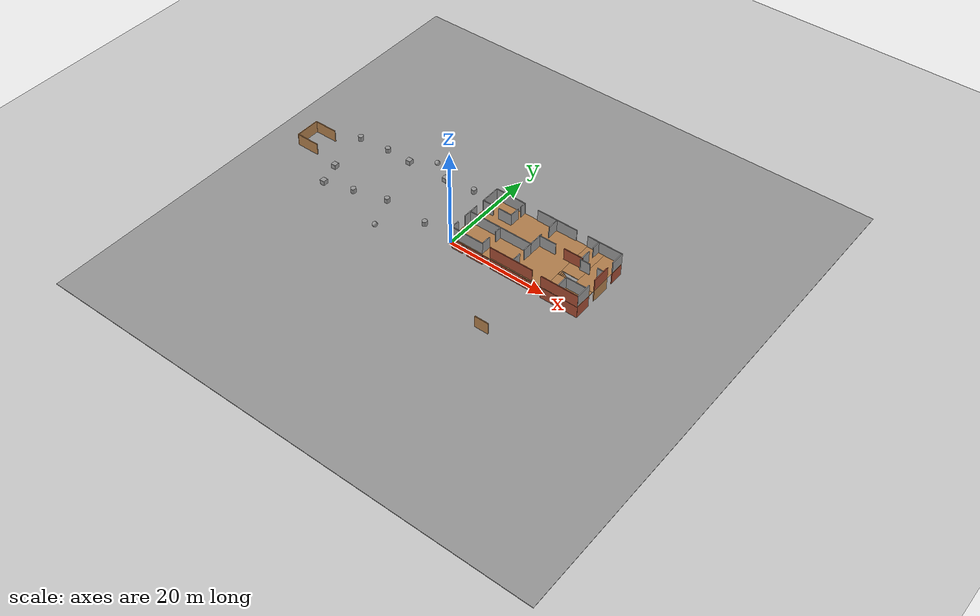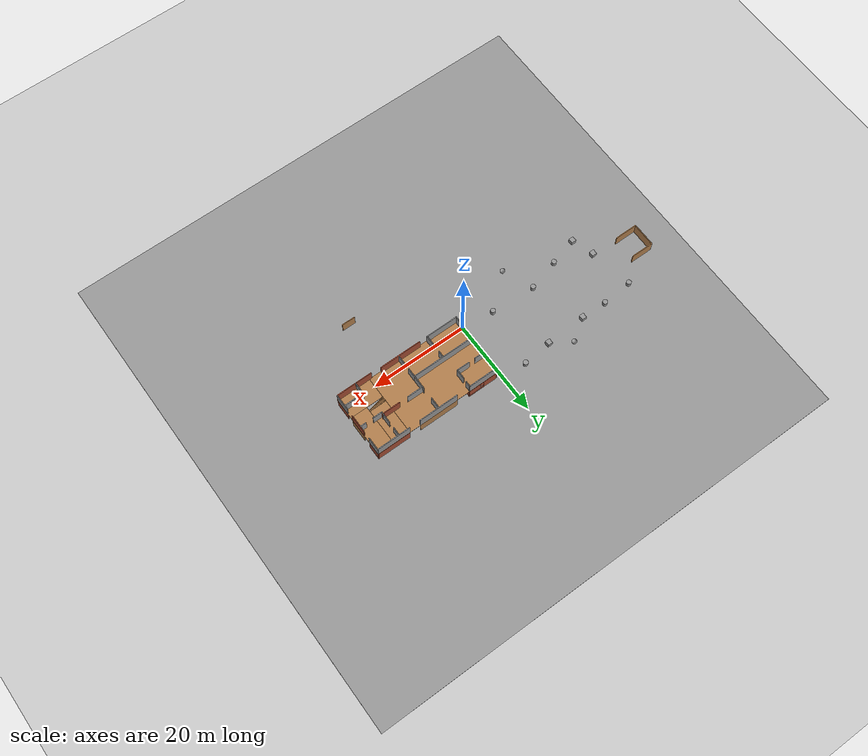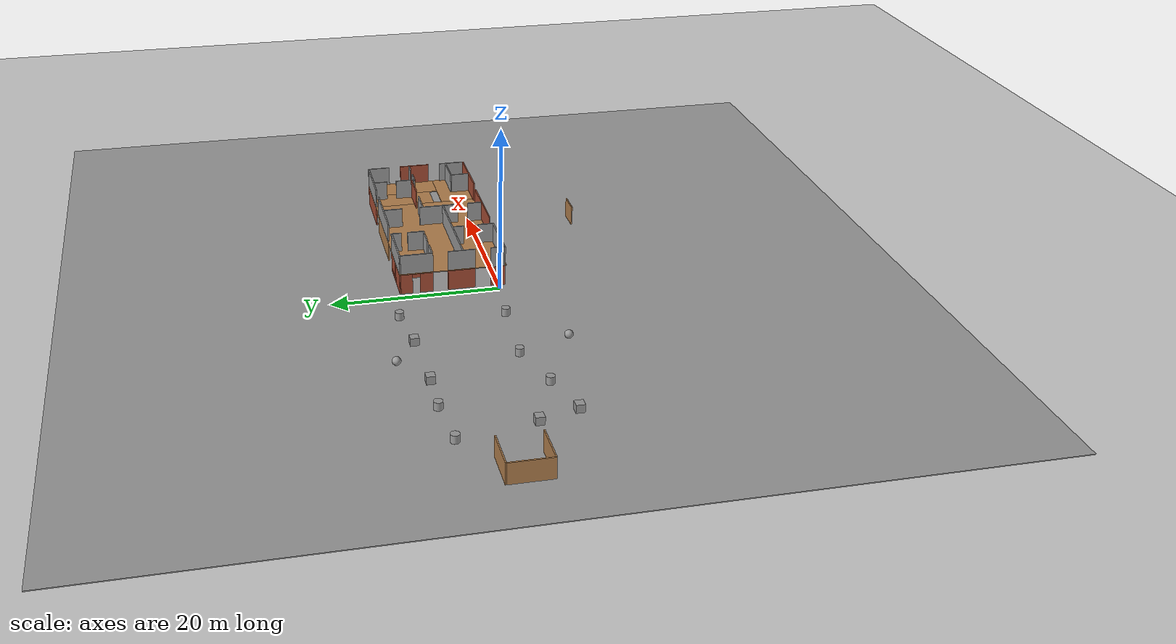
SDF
<sdf version="1.7">
 <world name="default">
  <light name="sun" type="directional">
   <pose>0 0 10 0 -0 0</pose>
   <diffuse>0.8 0.8 0.8 1</diffuse>
   <specular>0.2 0.2 0.2 1</specular>
   <attenuation>
    <range>1000</range>
    <constant>0.9</constant>
    <linear>0.01</linear>
    <quadratic>0.001</quadratic>
   </attenuation>
   <direction>-0.5 0.1 -0.9</direction>
   <spot><inner_angle>0</inner_angle><outer_angle>0</outer_angle><falloff>0</falloff></spot>
  </light>
  <model name="ground_plane">
   <static>1</static>
   <link name="link">
    <collision name="collision">
     <geometry><plane><normal>0 0 1</normal><size>100 100</size></plane></geometry>
     <surface><friction><ode><mu>100</mu><mu2>50</mu2></ode></friction></surface>
    </collision>
    <visual name="visual">
     <cast_shadows>0</cast_shadows>
     <geometry><plane><normal>0 0 1</normal><size>100 100</size></plane></geometry>
     <material>
      <script><uri>file://media/materials/scripts/gazebo.material</uri><name>Gazebo/Grey</name></script>
     </material>
    </visual>
   </link>
  </model>
  <gravity>0 0 -9.8</gravity>
  <magnetic_field>6e-06 2.3e-05 -4.2e-05</magnetic_field>
  <atmosphere type="adiabatic"/>
  <physics type="ode">
   <max_step_size>0.001</max_step_size>
   <real_time_factor>1</real_time_factor>
   <real_time_update_rate>1000</real_time_update_rate>
  </physics>
  <scene><ambient>0.4 0.4 0.4 1</ambient><background>0.7 0.7 0.7 1</background><shadows>1</shadows></scene>
  <spherical_coordinates>
   <surface_model>EARTH_WGS84</surface_model>
   <latitude_deg>0</latitude_deg>
   <longitude_deg>0</longitude_deg>
   <elevation>0</elevation>
   <heading_deg>0</heading_deg>
  </spherical_coordinates>
  <model name="new_world">
   <pose>-5.7411 -0.55673 0 0 -0 0</pose>
   <link name="Floor_3">
    <pose>19.9287 5.96658 2.5 0 -0 0</pose>
    <visual name="Floor_3_Visual_0">
     <pose>-3.49208 0 0.05 0 -0 0</pose>
     <geometry><box><size>19.5667 12.7728 0.1</size></box></geometry>
     <material>
      <script><uri>file://media/materials/scripts/gazebo.material</uri><name>Gazebo/Wood</name></script>
      <ambient>1 1 1 1</ambient>
     </material>
     <meta><layer>1</layer></meta>
    </visual>
    <collision name="Floor_3_Collision_0">
     <geometry><box><size>19.5667 12.7728 0.1</size></box></geometry>
     <pose>-3.49208 0 0.05 0 -0 0</pose>
    </collision>
    <visual name="Floor_3_Visual_1">
     <pose>9.78335 -4.25673 0.05 0 -0 0</pose>
     <geometry><box><size>6.98416 4.25935 0.1</size></box></geometry>
     <material>
      <script><uri>file://media/materials/scripts/gazebo.material</uri><name>Gazebo/Wood</name></script>
      <ambient>1 1 1 1</ambient>
     </material>
     <meta><layer>1</layer></meta>
    </visual>
    <collision name="Floor_3_Collision_1">
     <geometry><box><size>6.98416 4.25935 0.1</size></box></geometry>
     <pose>9.78335 -4.25673 0.05 0 -0 0</pose>
    </collision>
    <visual name="Floor_3_Visual_2">
     <pose>11.5333 2.12967 0.05 0 -0 0</pose>
     <geometry><box><size>3.48416 8.51345 0.1</size></box></geometry>
     <material>
      <script><uri>file://media/materials/scripts/gazebo.material</uri><name>Gazebo/Wood</name></script>
      <ambient>1 1 1 1</ambient>
     </material>
     <meta><layer>1</layer></meta>
    </visual>
    <collision name="Floor_3_Collision_2">
     <geometry><box><size>3.48416 8.51345 0.1</size></box></geometry>
     <pose>11.5333 2.12967 0.05 0 -0 0</pose>
    </collision>
    <visual name="Floor_3_Visual_3">
     <pose>8.04127 2.62967 0.05 0 -0 0</pose>
     <geometry><box><size>3.5 7.51345 0.1</size></box></geometry>
     <material>
      <script><uri>file://media/materials/scripts/gazebo.material</uri><name>Gazebo/Wood</name></script>
      <ambient>1 1 1 1</ambient>
     </material>
     <meta><layer>1</layer></meta>
    </visual>
    <collision name="Floor_3_Collision_3">
     <geometry><box><size>3.5 7.51345 0.1</size></box></geometry>
     <pose>8.04127 2.62967 0.05 0 -0 0</pose>
    </collision>
   </link>
   <link name="Stairs_4">
    <visual name="Stairs_4_Visual_0">
     <pose>29.6033 4.33952 0.083333 0 -0 -1.5708</pose>
     <geometry><box><size>1 0.233333 0.166667</size></box></geometry>
     <material>
      <script><uri>file://media/materials/scripts/gazebo.material</uri><name>Gazebo/Wood</name></script>
      <ambient>1 1 1 1</ambient>
     </material>
     <meta><layer>0</layer></meta>
    </visual>
    <collision name="Stairs_4_Collision_0">
     <geometry><box><size>1 0.233333 0.166667</size></box></geometry>
     <pose>29.6033 4.33952 0.083333 0 -0 -1.5708</pose>
    </collision>
    <visual name="Stairs_4_Visual_1">
     <pose>29.3699 4.33952 0.25 0 -0 -1.5708</pose>
     <geometry><box><size>1 0.233333 0.166667</size></box></geometry>
     <material>
      <script><uri>file://media/materials/scripts/gazebo.material</uri><name>Gazebo/Wood</name></script>
      <ambient>1 1 1 1</ambient>
     </material>
     <meta><layer>0</layer></meta>
    </visual>
    <collision name="Stairs_4_Collision_1">
     <geometry><box><size>1 0.233333 0.166667</size></box></geometry>
     <pose>29.3699 4.33952 0.25 0 -0 -1.5708</pose>
    </collision>
    <visual name="Stairs_4_Visual_2">
     <pose>29.1366 4.33952 0.416667 0 -0 -1.5708</pose>
     <geometry><box><size>1 0.233333 0.166667</size></box></geometry>
     <material>
      <script><uri>file://media/materials/scripts/gazebo.material</uri><name>Gazebo/Wood</name></script>
      <ambient>1 1 1 1</ambient>
     </material>
     <meta><layer>0</layer></meta>
    </visual>
    <collision name="Stairs_4_Collision_2">
     <geometry><box><size>1 0.233333 0.166667</size></box></geometry>
     <pose>29.1366 4.33952 0.416667 0 -0 -1.5708</pose>
    </collision>
    <visual name="Stairs_4_Visual_3">
     <pose>28.9033 4.33952 0.583333 0 -0 -1.5708</pose>
     <geometry><box><size>1 0.233333 0.166667</size></box></geometry>
     <material>
      <script><uri>file://media/materials/scripts/gazebo.material</uri><name>Gazebo/Wood</name></script>
      <ambient>1 1 1 1</ambient>
     </material>
     <meta><layer>0</layer></meta>
    </visual>
    <collision name="Stairs_4_Collision_3">
     <geometry><box><size>1 0.233333 0.166667</size></box></geometry>
     <pose>28.9033 4.33952 0.583333 0 -0 -1.5708</pose>
    </collision>
    <visual name="Stairs_4_Visual_4">
     <pose>28.6699 4.33952 0.75 0 -0 -1.5708</pose>
     <geometry><box><size>1 0.233333 0.166667</size></box></geometry>
     <material>
      <script><uri>file://media/materials/scripts/gazebo.material</uri><name>Gazebo/Wood</name></script>
      <ambient>1 1 1 1</ambient>
     </material>
     <meta><layer>0</layer></meta>
    </visual>
    <collision name="Stairs_4_Collision_4">
     <geometry><box><size>1 0.233333 0.166667</size></box></geometry>
     <pose>28.6699 4.33952 0.75 0 -0 -1.5708</pose>
    </collision>
    <visual name="Stairs_4_Visual_5">
     <pose>28.4366 4.33952 0.916667 0 -0 -1.5708</pose>
     <geometry><box><size>1 0.233333 0.166667</size></box></geometry>
     <material>
      <script><uri>file://media/materials/scripts/gazebo.material</uri><name>Gazebo/Wood</name></script>
      <ambient>1 1 1 1</ambient>
     </material>
     <meta><layer>0</layer></meta>
    </visual>
    <collision name="Stairs_4_Collision_5">
     <geometry><box><size>1 0.233333 0.166667</size></box></geometry>
     <pose>28.4366 4.33952 0.916667 0 -0 -1.5708</pose>
    </collision>
    <visual name="Stairs_4_Visual_6">
     <pose>28.2033 4.33952 1.08333 0 -0 -1.5708</pose>
     <geometry><box><size>1 0.233333 0.166667</size></box></geometry>
     <material>
      <script><uri>file://media/materials/scripts/gazebo.material</uri><name>Gazebo/Wood</name></script>
      <ambient>1 1 1 1</ambient>
     </material>
     <meta><layer>0</layer></meta>
    </visual>
    <collision name="Stairs_4_Collision_6">
     <geometry><box><size>1 0.233333 0.166667</size></box></geometry>
     <pose>28.2033 4.33952 1.08333 0 -0 -1.5708</pose>
    </collision>
    <visual name="Stairs_4_Visual_7">
     <pose>27.9699 4.33952 1.25 0 -0 -1.5708</pose>
     <geometry><box><size>1 0.233333 0.166667</size></box></geometry>
     <material>
      <script><uri>file://media/materials/scripts/gazebo.material</uri><name>Gazebo/Wood</name></script>
      <ambient>1 1 1 1</ambient>
     </material>
     <meta><layer>0</layer></meta>
    </visual>
    <collision name="Stairs_4_Collision_7">
     <geometry><box><size>1 0.233333 0.166667</size></box></geometry>
     <pose>27.9699 4.33952 1.25 0 -0 -1.5708</pose>
    </collision>
    <visual name="Stairs_4_Visual_8">
     <pose>27.7366 4.33952 1.41667 0 -0 -1.5708</pose>
     <geometry><box><size>1 0.233333 0.166667</size></box></geometry>
     <material>
      <script><uri>file://media/materials/scripts/gazebo.material</uri><name>Gazebo/Wood</name></script>
      <ambient>1 1 1 1</ambient>
     </material>
     <meta><layer>0</layer></meta>
    </visual>
    <collision name="Stairs_4_Collision_8">
     <geometry><box><size>1 0.233333 0.166667</size></box></geometry>
     <pose>27.7366 4.33952 1.41667 0 -0 -1.5708</pose>
    </collision>
    <visual name="Stairs_4_Visual_9">
     <pose>27.5033 4.33952 1.58333 0 -0 -1.5708</pose>
     <geometry><box><size>1 0.233333 0.166667</size></box></geometry>
     <material>
      <script><uri>file://media/materials/scripts/gazebo.material</uri><name>Gazebo/Wood</name></script>
      <ambient>1 1 1 1</ambient>
     </material>
     <meta><layer>0</layer></meta>
    </visual>
    <collision name="Stairs_4_Collision_9">
     <geometry><box><size>1 0.233333 0.166667</size></box></geometry>
     <pose>27.5033 4.33952 1.58333 0 -0 -1.5708</pose>
    </collision>
    <visual name="Stairs_4_Visual_10">
     <pose>27.2699 4.33952 1.75 0 -0 -1.5708</pose>
     <geometry><box><size>1 0.233333 0.166667</size></box></geometry>
     <material>
      <script><uri>file://media/materials/scripts/gazebo.material</uri><name>Gazebo/Wood</name></script>
      <ambient>1 1 1 1</ambient>
     </material>
     <meta><layer>0</layer></meta>
    </visual>
    <collision name="Stairs_4_Collision_10">
     <geometry><box><size>1 0.233333 0.166667</size></box></geometry>
     <pose>27.2699 4.33952 1.75 0 -0 -1.5708</pose>
    </collision>
    <visual name="Stairs_4_Visual_11">
     <pose>27.0366 4.33952 1.91667 0 -0 -1.5708</pose>
     <geometry><box><size>1 0.233333 0.166667</size></box></geometry>
     <material>
      <script><uri>file://media/materials/scripts/gazebo.material</uri><name>Gazebo/Wood</name></script>
      <ambient>1 1 1 1</ambient>
     </material>
     <meta><layer>0</layer></meta>
    </visual>
    <collision name="Stairs_4_Collision_11">
     <geometry><box><size>1 0.233333 0.166667</size></box></geometry>
     <pose>27.0366 4.33952 1.91667 0 -0 -1.5708</pose>
    </collision>
    <visual name="Stairs_4_Visual_12">
     <pose>26.8033 4.33952 2.08333 0 -0 -1.5708</pose>
     <geometry><box><size>1 0.233333 0.166667</size></box></geometry>
     <material>
      <script><uri>file://media/materials/scripts/gazebo.material</uri><name>Gazebo/Wood</name></script>
      <ambient>1 1 1 1</ambient>
     </material>
     <meta><layer>0</layer></meta>
    </visual>
    <collision name="Stairs_4_Collision_12">
     <geometry><box><size>1 0.233333 0.166667</size></box></geometry>
     <pose>26.8033 4.33952 2.08333 0 -0 -1.5708</pose>
    </collision>
    <visual name="Stairs_4_Visual_13">
     <pose>26.5699 4.33952 2.25 0 -0 -1.5708</pose>
     <geometry><box><size>1 0.233333 0.166667</size></box></geometry>
     <material>
      <script><uri>file://media/materials/scripts/gazebo.material</uri><name>Gazebo/Wood</name></script>
      <ambient>1 1 1 1</ambient>
     </material>
     <meta><layer>0</layer></meta>
    </visual>
    <collision name="Stairs_4_Collision_13">
     <geometry><box><size>1 0.233333 0.166667</size></box></geometry>
     <pose>26.5699 4.33952 2.25 0 -0 -1.5708</pose>
    </collision>
    <visual name="Stairs_4_Visual_14">
     <pose>26.3366 4.33952 2.41667 0 -0 -1.5708</pose>
     <geometry><box><size>1 0.233333 0.166667</size></box></geometry>
     <material>
      <script><uri>file://media/materials/scripts/gazebo.material</uri><name>Gazebo/Wood</name></script>
      <ambient>1 1 1 1</ambient>
     </material>
     <meta><layer>0</layer></meta>
    </visual>
    <collision name="Stairs_4_Collision_14">
     <geometry><box><size>1 0.233333 0.166667</size></box></geometry>
     <pose>26.3366 4.33952 2.41667 0 -0 -1.5708</pose>
    </collision>
   </link>
   <link name="Wall_15">
    <pose>9.82012 12.272 0 0 -0 0</pose>
    <visual name="Wall_15_Visual_0">
     <pose>-1.65398 0 1.25 0 -0 0</pose>
     <geometry><box><size>2.94205 0.15 2.5</size></box></geometry>
     <material>
      <script><uri>file://media/materials/scripts/gazebo.material</uri><name>Gazebo/Bricks</name></script>
      <ambient>1 1 1 1</ambient>
     </material>
     <meta><layer>0</layer></meta>
    </visual>
    <collision name="Wall_15_Collision_0">
     <geometry><box><size>2.94205 0.15 2.5</size></box></geometry>
     <pose>-1.65398 0 1.25 0 -0 0</pose>
    </collision>
    <visual name="Wall_15_Visual_1">
     <pose>1.47102 0 0.25 0 -0 0</pose>
     <geometry><box><size>3.30795 0.15 0.5</size></box></geometry>
     <material>
      <script><uri>file://media/materials/scripts/gazebo.material</uri><name>Gazebo/Bricks</name></script>
      <ambient>1 1 1 1</ambient>
     </material>
     <meta><layer>0</layer></meta>
    </visual>
    <collision name="Wall_15_Collision_1">
     <geometry><box><size>3.30795 0.15 0.5</size></box></geometry>
     <pose>1.47102 0 0.25 0 -0 0</pose>
    </collision>
    <visual name="Wall_15_Visual_2">
     <pose>1.87102 0 1.5 0 -0 0</pose>
     <geometry><box><size>2.50795 0.15 2</size></box></geometry>
     <material>
      <script><uri>file://media/materials/scripts/gazebo.material</uri><name>Gazebo/Bricks</name></script>
      <ambient>1 1 1 1</ambient>
     </material>
     <meta><layer>0</layer></meta>
    </visual>
    <collision name="Wall_15_Collision_2">
     <geometry><box><size>2.50795 0.15 2</size></box></geometry>
     <pose>1.87102 0 1.5 0 -0 0</pose>
    </collision>
    <visual name="Wall_15_Visual_3">
     <pose>0.217048 0 1.9 0 -0 0</pose>
     <geometry><box><size>0.8 0.15 1.2</size></box></geometry>
     <material>
      <script><uri>file://media/materials/scripts/gazebo.material</uri><name>Gazebo/Bricks</name></script>
      <ambient>1 1 1 1</ambient>
     </material>
     <meta><layer>0</layer></meta>
    </visual>
    <collision name="Wall_15_Collision_3">
     <geometry><box><size>0.8 0.15 1.2</size></box></geometry>
     <pose>0.217048 0 1.9 0 -0 0</pose>
    </collision>
   </link>
   <link name="Wall_166">
    <collision name="Wall_166_Collision">
     <geometry><box><size>6.25 0.15 2.5</size></box></geometry>
     <pose>0 0 1.25 0 -0 0</pose>
    </collision>
    <visual name="Wall_166_Visual">
     <pose>0 0 1.25 0 -0 0</pose>
     <geometry><box><size>6.25 0.15 2.5</size></box></geometry>
     <material>
      <script><uri>file://media/materials/scripts/gazebo.material</uri><name>Gazebo/Grey</name></script>
      <ambient>1 1 1 1</ambient>
     </material>
     <meta><layer>1</layer></meta>
    </visual>
    <pose>9.82012 12.272 2.5 0 -0 0</pose>
   </link>
   <link name="Wall_167">
    <collision name="Wall_167_Collision">
     <geometry><box><size>7.5 0.15 2.5</size></box></geometry>
     <pose>0 0 1.25 0 -0 0</pose>
    </collision>
    <visual name="Wall_167_Visual">
     <pose>0 0 1.25 0 -0 0</pose>
     <geometry><box><size>7.5 0.15 2.5</size></box></geometry>
     <material>
      <script><uri>file://media/materials/scripts/gazebo.material</uri><name>Gazebo/Bricks</name></script>
      <ambient>1 1 1 1</ambient>
     </material>
     <meta><layer>1</layer></meta>
    </visual>
    <pose>29.4319 -0.344823 2.5 0 -0 0</pose>
   </link>
   <link name="Wall_168">
    <collision name="Wall_168_Collision">
     <geometry><box><size>2.75 0.15 2.5</size></box></geometry>
     <pose>0 0 1.25 0 -0 0</pose>
    </collision>
    <visual name="Wall_168_Visual">
     <pose>0 0 1.25 0 -0 0</pose>
     <geometry><box><size>2.75 0.15 2.5</size></box></geometry>
     <material>
      <script><uri>file://media/materials/scripts/gazebo.material</uri><name>Gazebo/Grey</name></script>
      <ambient>1 1 1 1</ambient>
     </material>
     <meta><layer>1</layer></meta>
    </visual>
    <pose>33.1201 10.972 2.5 0 -0 -1.5708</pose>
   </link>
   <link name="Wall_169">
    <collision name="Wall_169_Collision">
     <geometry><box><size>3.75 0.15 2.5</size></box></geometry>
     <pose>0 0 1.25 0 -0 0</pose>
    </collision>
    <visual name="Wall_169_Visual">
     <pose>0 0 1.25 0 -0 0</pose>
     <geometry><box><size>3.75 0.15 2.5</size></box></geometry>
     <material>
      <script><uri>file://media/materials/scripts/gazebo.material</uri><name>Gazebo/Bricks</name></script>
      <ambient>1 1 1 1</ambient>
     </material>
     <meta><layer>1</layer></meta>
    </visual>
    <pose>33.1291 6.22555 2.5 0 -0 -1.5708</pose>
   </link>
   <link name="Wall_170">
    <collision name="Wall_170_Collision">
     <geometry><box><size>3.25 0.15 2.5</size></box></geometry>
     <pose>0 0 1.25 0 -0 0</pose>
    </collision>
    <visual name="Wall_170_Visual">
     <pose>0 0 1.25 0 -0 0</pose>
     <geometry><box><size>3.25 0.15 2.5</size></box></geometry>
     <material>
      <script><uri>file://media/materials/scripts/gazebo.material</uri><name>Gazebo/Grey</name></script>
      <ambient>1 1 1 1</ambient>
     </material>
     <meta><layer>1</layer></meta>
    </visual>
    <pose>33.1091 1.23835 2.5 0 -0 -1.5708</pose>
   </link>
   <link name="Wall_171">
    <collision name="Wall_171_Collision">
     <geometry><box><size>4 0.15 2.5</size></box></geometry>
     <pose>0 0 1.25 0 -0 0</pose>
    </collision>
    <visual name="Wall_171_Visual">
     <pose>0 0 1.25 0 -0 0</pose>
     <geometry><box><size>4 0.15 2.5</size></box></geometry>
     <material>
      <script><uri>file://media/materials/scripts/gazebo.material</uri><name>Gazebo/Grey</name></script>
      <ambient>1 1 1 1</ambient>
     </material>
     <meta><layer>1</layer></meta>
    </visual>
    <pose>6.77012 10.347 2.5 0 -0 -1.5708</pose>
   </link>
   <link name="Wall_172">
    <collision name="Wall_172_Collision">
     <geometry><box><size>3.25 0.15 2.5</size></box></geometry>
     <pose>0 0 1.25 0 -0 0</pose>
    </collision>
    <visual name="Wall_172_Visual">
     <pose>0 0 1.25 0 -0 0</pose>
     <geometry><box><size>3.25 0.15 2.5</size></box></geometry>
     <material>
      <script><uri>file://media/materials/scripts/gazebo.material</uri><name>Gazebo/Grey</name></script>
      <ambient>1 1 1 1</ambient>
     </material>
     <meta><layer>1</layer></meta>
    </visual>
    <pose>6.75883 4.95214 2.5 0 -0 -1.5708</pose>
   </link>
   <link name="Wall_173">
    <collision name="Wall_173_Collision">
     <geometry><box><size>1.75 0.15 2.5</size></box></geometry>
     <pose>0 0 1.25 0 -0 0</pose>
    </collision>
    <visual name="Wall_173_Visual">
     <pose>0 0 1.25 0 -0 0</pose>
     <geometry><box><size>1.75 0.15 2.5</size></box></geometry>
     <material>
      <script><uri>file://media/materials/scripts/gazebo.material</uri><name>Gazebo/Grey</name></script>
      <ambient>1 1 1 1</ambient>
     </material>
     <meta><layer>1</layer></meta>
    </visual>
    <pose>6.72823 0.593575 2.5 0 -0 -1.5708</pose>
   </link>
   <link name="Wall_174">
    <collision name="Wall_174_Collision">
     <geometry><box><size>8.25 0.15 2.5</size></box></geometry>
     <pose>0 0 1.25 0 -0 0</pose>
    </collision>
    <visual name="Wall_174_Visual">
     <pose>0 0 1.25 0 -0 0</pose>
     <geometry><box><size>8.25 0.15 2.5</size></box></geometry>
     <material>
      <script><uri>file://media/materials/scripts/gazebo.material</uri><name>Gazebo/Grey</name></script>
      <ambient>1 1 1 1</ambient>
     </material>
     <meta><layer>1</layer></meta>
    </visual>
    <pose>19.8006 12.278 2.5 0 -0 0</pose>
   </link>
   <link name="Wall_175">
    <collision name="Wall_175_Collision">
     <geometry><box><size>7 0.15 2.5</size></box></geometry>
     <pose>0 0 1.25 0 -0 0</pose>
    </collision>
    <visual name="Wall_175_Visual">
     <pose>0 0 1.25 0 -0 0</pose>
     <geometry><box><size>7 0.15 2.5</size></box></geometry>
     <material>
      <script><uri>file://media/materials/scripts/gazebo.material</uri><name>Gazebo/Grey</name></script>
      <ambient>1 1 1 1</ambient>
     </material>
     <meta><layer>1</layer></meta>
    </visual>
    <pose>29.6951 12.272 2.5 0 -0 3.14159</pose>
   </link>
   <link name="Wall_176">
    <collision name="Wall_176_Collision">
     <geometry><box><size>6.75 0.15 2.5</size></box></geometry>
     <pose>0 0 1.25 0 -0 0</pose>
    </collision>
    <visual name="Wall_176_Visual">
     <pose>0 0 1.25 0 -0 0</pose>
     <geometry><box><size>6.75 0.15 2.5</size></box></geometry>
     <material>
      <script><uri>file://media/materials/scripts/gazebo.material</uri><name>Gazebo/Grey</name></script>
      <ambient>1 1 1 1</ambient>
     </material>
     <meta><layer>1</layer></meta>
    </visual>
    <pose>10.0282 -0.206425 2.5 0 -0 0</pose>
   </link>
   <link name="Wall_177">
    <collision name="Wall_177_Collision">
     <geometry><box><size>8.75 0.15 2.5</size></box></geometry>
     <pose>0 0 1.25 0 -0 0</pose>
    </collision>
    <visual name="Wall_177_Visual">
     <pose>0 0 1.25 0 -0 0</pose>
     <geometry><box><size>8.75 0.15 2.5</size></box></geometry>
     <material>
      <script><uri>file://media/materials/scripts/gazebo.material</uri><name>Gazebo/Bricks</name></script>
      <ambient>1 1 1 1</ambient>
     </material>
     <meta><layer>1</layer></meta>
    </visual>
    <pose>19.3774 -0.149946 2.5 0 -0 0</pose>
   </link>
   <link name="Wall_178">
    <collision name="Wall_178_Collision">
     <geometry><box><size>2.25 0.15 2.5</size></box></geometry>
     <pose>0 0 1.25 0 -0 0</pose>
    </collision>
    <visual name="Wall_178_Visual">
     <pose>0 0 1.25 0 -0 0</pose>
     <geometry><box><size>2.25 0.15 2.5</size></box></geometry>
     <material>
      <script><uri>file://media/materials/scripts/gazebo.material</uri><name>Gazebo/Grey</name></script>
      <ambient>1 1 1 1</ambient>
     </material>
     <meta><layer>1</layer></meta>
    </visual>
    <pose>7.82012 8.42205 2.5 0 -0 0</pose>
   </link>
   <link name="Wall_179">
    <collision name="Wall_179_Collision">
     <geometry><box><size>2 0.15 2.5</size></box></geometry>
     <pose>0 0 1.25 0 -0 0</pose>
    </collision>
    <visual name="Wall_179_Visual">
     <pose>0 0 1.25 0 -0 0</pose>
     <geometry><box><size>2 0.15 2.5</size></box></geometry>
     <material>
      <script><uri>file://media/materials/scripts/gazebo.material</uri><name>Gazebo/Grey</name></script>
      <ambient>1 1 1 1</ambient>
     </material>
     <meta><layer>1</layer></meta>
    </visual>
    <pose>12.8315 9.36573 2.5 0 -0 1.5708</pose>
   </link>
   <link name="Wall_180">
    <collision name="Wall_180_Collision">
     <geometry><box><size>1.25 0.15 2.5</size></box></geometry>
     <pose>0 0 1.25 0 -0 0</pose>
    </collision>
    <visual name="Wall_180_Visual">
     <pose>0 0 1.25 0 -0 0</pose>
     <geometry><box><size>1.25 0.15 2.5</size></box></geometry>
     <material>
      <script><uri>file://media/materials/scripts/gazebo.material</uri><name>Gazebo/Grey</name></script>
      <ambient>1 1 1 1</ambient>
     </material>
     <meta><layer>1</layer></meta>
    </visual>
    <pose>12.8701 11.722 2.5 0 -0 1.5708</pose>
   </link>
   <link name="Wall_181">
    <collision name="Wall_181_Collision">
     <geometry><box><size>2.75 0.15 2.5</size></box></geometry>
     <pose>0 0 1.25 0 -0 0</pose>
    </collision>
    <visual name="Wall_181_Visual">
     <pose>0 0 1.25 0 -0 0</pose>
     <geometry><box><size>2.75 0.15 2.5</size></box></geometry>
     <material>
      <script><uri>file://media/materials/scripts/gazebo.material</uri><name>Gazebo/Grey</name></script>
      <ambient>1 1 1 1</ambient>
     </material>
     <meta><layer>1</layer></meta>
    </visual>
    <pose>11.5201 8.42205 2.5 0 -0 0</pose>
   </link>
   <link name="Wall_182">
    <collision name="Wall_182_Collision">
     <geometry><box><size>13 0.15 2.5</size></box></geometry>
     <pose>0 0 1.25 0 -0 0</pose>
    </collision>
    <visual name="Wall_182_Visual">
     <pose>0 0 1.25 0 -0 0</pose>
     <geometry><box><size>13 0.15 2.5</size></box></geometry>
     <material>
      <script><uri>file://media/materials/scripts/gazebo.material</uri><name>Gazebo/Grey</name></script>
      <ambient>1 1 1 1</ambient>
     </material>
     <meta><layer>1</layer></meta>
    </visual>
    <pose>13.3384 4.80537 2.5 0 -0 0</pose>
   </link>
   <link name="Wall_183">
    <collision name="Wall_183_Collision">
     <geometry><box><size>3 0.15 2.5</size></box></geometry>
     <pose>0 0 1.25 0 -0 0</pose>
    </collision>
    <visual name="Wall_183_Visual">
     <pose>0 0 1.25 0 -0 0</pose>
     <geometry><box><size>3 0.15 2.5</size></box></geometry>
     <material>
      <script><uri>file://media/materials/scripts/gazebo.material</uri><name>Gazebo/Grey</name></script>
      <ambient>1 1 1 1</ambient>
     </material>
     <meta><layer>1</layer></meta>
    </visual>
    <pose>19.7634 6.23037 2.5 0 -0 1.5708</pose>
   </link>
   <link name="Wall_184">
    <collision name="Wall_184_Collision">
     <geometry><box><size>2.25 0.15 2.5</size></box></geometry>
     <pose>0 0 1.25 0 -0 0</pose>
    </collision>
    <visual name="Wall_184_Visual">
     <pose>0 0 1.25 0 -0 0</pose>
     <geometry><box><size>2.25 0.15 2.5</size></box></geometry>
     <material>
      <script><uri>file://media/materials/scripts/gazebo.material</uri><name>Gazebo/Grey</name></script>
      <ambient>1 1 1 1</ambient>
     </material>
     <meta><layer>1</layer></meta>
    </visual>
    <pose>19.7634 11.0554 2.5 0 -0 1.5708</pose>
   </link>
   <link name="Wall_185">
    <collision name="Wall_185_Collision">
     <geometry><box><size>2 0.15 2.5</size></box></geometry>
     <pose>0 0 1.25 0 -0 0</pose>
    </collision>
    <visual name="Wall_185_Visual">
     <pose>0 0 1.25 0 -0 0</pose>
     <geometry><box><size>2 0.15 2.5</size></box></geometry>
     <material>
      <script><uri>file://media/materials/scripts/gazebo.material</uri><name>Gazebo/Grey</name></script>
      <ambient>1 1 1 1</ambient>
     </material>
     <meta><layer>1</layer></meta>
    </visual>
    <pose>13.3282 0.718575 2.5 0 -0 1.5708</pose>
   </link>
   <link name="Wall_186">
    <collision name="Wall_186_Collision">
     <geometry><box><size>1.25 0.15 2.5</size></box></geometry>
     <pose>0 0 1.25 0 -0 0</pose>
    </collision>
    <visual name="Wall_186_Visual">
     <pose>0 0 1.25 0 -0 0</pose>
     <geometry><box><size>1.25 0.15 2.5</size></box></geometry>
     <material>
      <script><uri>file://media/materials/scripts/gazebo.material</uri><name>Gazebo/Grey</name></script>
      <ambient>1 1 1 1</ambient>
     </material>
     <meta><layer>1</layer></meta>
    </visual>
    <pose>13.3282 4.04357 2.5 0 -0 1.5708</pose>
   </link>
   <link name="Wall_187">
    <collision name="Wall_187_Collision">
     <geometry><box><size>2 0.15 2.5</size></box></geometry>
     <pose>0 0 1.25 0 -0 0</pose>
    </collision>
    <visual name="Wall_187_Visual">
     <pose>0 0 1.25 0 -0 0</pose>
     <geometry><box><size>2 0.15 2.5</size></box></geometry>
     <material>
      <script><uri>file://media/materials/scripts/gazebo.material</uri><name>Gazebo/Grey</name></script>
      <ambient>1 1 1 1</ambient>
     </material>
     <meta><layer>1</layer></meta>
    </visual>
    <pose>19.7634 3.88037 2.5 0 -0 -1.5708</pose>
   </link>
   <link name="Wall_188">
    <collision name="Wall_188_Collision">
     <geometry><box><size>1.75 0.15 2.5</size></box></geometry>
     <pose>0 0 1.25 0 -0 0</pose>
    </collision>
    <visual name="Wall_188_Visual">
     <pose>0 0 1.25 0 -0 0</pose>
     <geometry><box><size>1.75 0.15 2.5</size></box></geometry>
     <material>
      <script><uri>file://media/materials/scripts/gazebo.material</uri><name>Gazebo/Grey</name></script>
      <ambient>1 1 1 1</ambient>
     </material>
     <meta><layer>1</layer></meta>
    </visual>
    <pose>19.7634 0.805366 2.5 0 -0 -1.5708</pose>
   </link>
   <link name="Wall_189">
    <collision name="Wall_189_Collision">
     <geometry><box><size>1.75 0.15 2.5</size></box></geometry>
     <pose>0 0 1.25 0 -0 0</pose>
    </collision>
    <visual name="Wall_189_Visual">
     <pose>0 0 1.25 0 -0 0</pose>
     <geometry><box><size>1.75 0.15 2.5</size></box></geometry>
     <material>
      <script><uri>file://media/materials/scripts/gazebo.material</uri><name>Gazebo/Grey</name></script>
      <ambient>1 1 1 1</ambient>
     </material>
     <meta><layer>1</layer></meta>
    </visual>
    <pose>28.489 11.4409 2.5 0 -0 -1.5708</pose>
   </link>
   <link name="Wall_19">
    <collision name="Wall_19_Collision">
     <geometry><box><size>7.5 0.15 2.5</size></box></geometry>
     <pose>0 0 1.25 0 -0 0</pose>
    </collision>
    <visual name="Wall_19_Visual">
     <pose>0 0 1.25 0 -0 0</pose>
     <geometry><box><size>7.5 0.15 2.5</size></box></geometry>
     <material>
      <script><uri>file://media/materials/scripts/gazebo.material</uri><name>Gazebo/Bricks</name></script>
      <ambient>1 1 1 1</ambient>
     </material>
     <meta><layer>0</layer></meta>
    </visual>
    <pose>29.4316 -0.345181 0 0 -0 0</pose>
   </link>
   <link name="Wall_190">
    <collision name="Wall_190_Collision">
     <geometry><box><size>2.5 0.15 2.5</size></box></geometry>
     <pose>0 0 1.25 0 -0 0</pose>
    </collision>
    <visual name="Wall_190_Visual">
     <pose>0 0 1.25 0 -0 0</pose>
     <geometry><box><size>2.5 0.15 2.5</size></box></geometry>
     <material>
      <script><uri>file://media/materials/scripts/gazebo.material</uri><name>Gazebo/Grey</name></script>
      <ambient>1 1 1 1</ambient>
     </material>
     <meta><layer>1</layer></meta>
    </visual>
    <pose>28.489 8.11594 2.5 0 -0 -1.5708</pose>
   </link>
   <link name="Wall_191">
    <collision name="Wall_191_Collision">
     <geometry><box><size>2 0.15 2.5</size></box></geometry>
     <pose>0 0 1.25 0 -0 0</pose>
    </collision>
    <visual name="Wall_191_Visual">
     <pose>0 0 1.25 0 -0 0</pose>
     <geometry><box><size>2 0.15 2.5</size></box></geometry>
     <material>
      <script><uri>file://media/materials/scripts/gazebo.material</uri><name>Gazebo/Grey</name></script>
      <ambient>1 1 1 1</ambient>
     </material>
     <meta><layer>1</layer></meta>
    </visual>
    <pose>29.414 6.94094 2.5 0 -0 0</pose>
   </link>
   <link name="Wall_192">
    <collision name="Wall_192_Collision">
     <geometry><box><size>1.25 0.15 2.5</size></box></geometry>
     <pose>0 0 1.25 0 -0 0</pose>
    </collision>
    <visual name="Wall_192_Visual">
     <pose>0 0 1.25 0 -0 0</pose>
     <geometry><box><size>1.25 0.15 2.5</size></box></geometry>
     <material>
      <script><uri>file://media/materials/scripts/gazebo.material</uri><name>Gazebo/Grey</name></script>
      <ambient>1 1 1 1</ambient>
     </material>
     <meta><layer>1</layer></meta>
    </visual>
    <pose>32.489 6.94094 2.5 0 -0 0</pose>
   </link>
   <link name="Wall_193">
    <collision name="Wall_193_Collision">
     <geometry><box><size>3.4468 0.15 2.5</size></box></geometry>
     <pose>0 0 1.25 0 -0 0</pose>
    </collision>
    <visual name="Wall_193_Visual">
     <pose>0 0 1.25 0 -0 0</pose>
     <geometry><box><size>3.4468 0.15 2.5</size></box></geometry>
     <material>
      <script><uri>file://media/materials/scripts/gazebo.material</uri><name>Gazebo/Grey</name></script>
      <ambient>1 1 1 1</ambient>
     </material>
     <meta><layer>1</layer></meta>
    </visual>
    <pose>21.4125 7.3199 2.5 0 -0 0</pose>
   </link>
   <link name="Wall_194">
    <collision name="Wall_194_Collision">
     <geometry><box><size>3.8032 0.15 2.5</size></box></geometry>
     <pose>0 0 1.25 0 -0 0</pose>
    </collision>
    <visual name="Wall_194_Visual">
     <pose>0 0 1.25 0 -0 0</pose>
     <geometry><box><size>3.8032 0.15 2.5</size></box></geometry>
     <material>
      <script><uri>file://media/materials/scripts/gazebo.material</uri><name>Gazebo/Bricks</name></script>
      <ambient>1 1 1 1</ambient>
     </material>
     <meta><layer>1</layer></meta>
    </visual>
    <pose>26.7375 7.3199 2.5 0 -0 0</pose>
   </link>
   <link name="Wall_199">
    <collision name="Wall_199_Collision">
     <geometry><box><size>4 0.15 2.5</size></box></geometry>
     <pose>0 0 1.25 0 -0 0</pose>
    </collision>
    <visual name="Wall_199_Visual">
     <pose>0 0 1.25 0 -0 0</pose>
     <geometry><box><size>4 0.15 2.5</size></box></geometry>
     <material>
      <script><uri>file://media/materials/scripts/gazebo.material</uri><name>Gazebo/Grey</name></script>
      <ambient>1 1 1 1</ambient>
     </material>
     <meta><layer>1</layer></meta>
    </visual>
    <pose>31.0314 2.04433 2.5 0 -0 0</pose>
   </link>
   <link name="Wall_200">
    <collision name="Wall_200_Collision">
     <geometry><box><size>2.5 0.15 2.5</size></box></geometry>
     <pose>0 0 1.25 0 -0 0</pose>
    </collision>
    <visual name="Wall_200_Visual">
     <pose>0 0 1.25 0 -0 0</pose>
     <geometry><box><size>2.5 0.15 2.5</size></box></geometry>
     <material>
      <script><uri>file://media/materials/scripts/gazebo.material</uri><name>Gazebo/Grey</name></script>
      <ambient>1 1 1 1</ambient>
     </material>
     <meta><layer>1</layer></meta>
    </visual>
    <pose>29.1064 0.869326 2.5 0 -0 -1.5708</pose>
   </link>
   <link name="Wall_208">
    <collision name="Wall_208_Collision">
     <geometry><box><size>2.75 0.15 2.5</size></box></geometry>
     <pose>0 0 1.25 0 -0 0</pose>
    </collision>
    <visual name="Wall_208_Visual">
     <pose>0 0 1.25 0 -0 0</pose>
     <geometry><box><size>2.75 0.15 2.5</size></box></geometry>
     <material>
      <script><uri>file://media/materials/scripts/gazebo.material</uri><name>Gazebo/Wood</name></script>
      <ambient>1 1 1 1</ambient>
     </material>
     <meta><layer>0</layer></meta>
    </visual>
    <pose>22.7009 -12.278 0 0 -0 0</pose>
   </link>
   <link name="Wall_21">
    <collision name="Wall_21_Collision">
     <geometry><box><size>2.75 0.15 2.5</size></box></geometry>
     <pose>0 0 1.25 0 -0 0</pose>
    </collision>
    <visual name="Wall_21_Visual">
     <pose>0 0 1.25 0 -0 0</pose>
     <geometry><box><size>2.75 0.15 2.5</size></box></geometry>
     <material>
      <script><uri>file://media/materials/scripts/gazebo.material</uri><name>Gazebo/Bricks</name></script>
      <ambient>1 1 1 1</ambient>
     </material>
     <meta><layer>0</layer></meta>
    </visual>
    <pose>33.1201 10.972 0 0 -0 -1.5708</pose>
   </link>
   <link name="Wall_216">
    <collision name="Wall_216_Collision">
     <geometry><box><size>4.75 0.15 2.5</size></box></geometry>
     <pose>0 0 1.25 0 -0 0</pose>
    </collision>
    <visual name="Wall_216_Visual">
     <pose>0 0 1.25 0 -0 0</pose>
     <geometry><box><size>4.75 0.15 2.5</size></box></geometry>
     <material>
      <script><uri>file://media/materials/scripts/gazebo.material</uri><name>Gazebo/Wood</name></script>
      <ambient>1 1 1 1</ambient>
     </material>
     <meta><layer>0</layer></meta>
    </visual>
    <pose>-30.8296 8.53108 0 0 -0 0</pose>
   </link>
   <link name="Wall_218">
    <collision name="Wall_218_Collision">
     <geometry><box><size>5 0.15 2.5</size></box></geometry>
     <pose>0 0 1.25 0 -0 0</pose>
    </collision>
    <visual name="Wall_218_Visual">
     <pose>0 0 1.25 0 -0 0</pose>
     <geometry><box><size>5 0.15 2.5</size></box></geometry>
     <material>
      <script><uri>file://media/materials/scripts/gazebo.material</uri><name>Gazebo/Wood</name></script>
      <ambient>1 1 1 1</ambient>
     </material>
     <meta><layer>0</layer></meta>
    </visual>
    <pose>-33.1296 6.10608 0 0 -0 -1.5708</pose>
   </link>
   <link name="Wall_219">
    <collision name="Wall_219_Collision">
     <geometry><box><size>4.75 0.15 2.5</size></box></geometry>
     <pose>0 0 1.25 0 -0 0</pose>
    </collision>
    <visual name="Wall_219_Visual">
     <pose>0 0 1.25 0 -0 0</pose>
     <geometry><box><size>4.75 0.15 2.5</size></box></geometry>
     <material>
      <script><uri>file://media/materials/scripts/gazebo.material</uri><name>Gazebo/Wood</name></script>
      <ambient>1 1 1 1</ambient>
     </material>
     <meta><layer>0</layer></meta>
    </visual>
    <pose>-30.8296 3.68108 0 0 -0 0</pose>
   </link>
   <link name="Wall_24">
    <collision name="Wall_24_Collision">
     <geometry><box><size>3.75 0.15 2.5</size></box></geometry>
     <pose>0 0 1.25 0 -0 0</pose>
    </collision>
    <visual name="Wall_24_Visual">
     <pose>0 0 1.25 0 -0 0</pose>
     <geometry><box><size>3.75 0.15 2.5</size></box></geometry>
     <material>
      <script><uri>file://media/materials/scripts/gazebo.material</uri><name>Gazebo/Wood</name></script>
      <ambient>1 1 1 1</ambient>
     </material>
     <meta><layer>0</layer></meta>
    </visual>
    <pose>33.1296 6.22582 0 0 -0 -1.5708</pose>
   </link>
   <link name="Wall_26">
    <collision name="Wall_26_Collision">
     <geometry><box><size>3.25 0.15 2.5</size></box></geometry>
     <pose>0 0 1.25 0 -0 0</pose>
    </collision>
    <visual name="Wall_26_Visual">
     <pose>0 0 1.25 0 -0 0</pose>
     <geometry><box><size>3.25 0.15 2.5</size></box></geometry>
     <material>
      <script><uri>file://media/materials/scripts/gazebo.material</uri><name>Gazebo/Bricks</name></script>
      <ambient>1 1 1 1</ambient>
     </material>
     <meta><layer>0</layer></meta>
    </visual>
    <pose>33.1096 1.23882 0 0 -0 -1.5708</pose>
   </link>
   <link name="Wall_28">
    <pose>6.77012 10.347 0 0 -0 -1.5708</pose>
    <visual name="Wall_28_Visual_0">
     <pose>-1.22892 0 1.25 0 -0 0</pose>
     <geometry><box><size>1.54216 0.15 2.5</size></box></geometry>
     <material>
      <script><uri>file://media/materials/scripts/gazebo.material</uri><name>Gazebo/Bricks</name></script>
      <ambient>1 1 1 1</ambient>
     </material>
     <meta><layer>0</layer></meta>
    </visual>
    <collision name="Wall_28_Collision_0">
     <geometry><box><size>1.54216 0.15 2.5</size></box></geometry>
     <pose>-1.22892 0 1.25 0 -0 0</pose>
    </collision>
    <visual name="Wall_28_Visual_1">
     <pose>1.22108 0 1.25 0 -0 0</pose>
     <geometry><box><size>1.55784 0.15 2.5</size></box></geometry>
     <material>
      <script><uri>file://media/materials/scripts/gazebo.material</uri><name>Gazebo/Bricks</name></script>
      <ambient>1 1 1 1</ambient>
     </material>
     <meta><layer>0</layer></meta>
    </visual>
    <collision name="Wall_28_Collision_1">
     <geometry><box><size>1.55784 0.15 2.5</size></box></geometry>
     <pose>1.22108 0 1.25 0 -0 0</pose>
    </collision>
    <visual name="Wall_28_Visual_2">
     <pose>-0.007843 0 2.25 0 -0 0</pose>
     <geometry><box><size>0.9 0.15 0.5</size></box></geometry>
     <material>
      <script><uri>file://media/materials/scripts/gazebo.material</uri><name>Gazebo/Bricks</name></script>
      <ambient>1 1 1 1</ambient>
     </material>
     <meta><layer>0</layer></meta>
    </visual>
    <collision name="Wall_28_Collision_2">
     <geometry><box><size>0.9 0.15 0.5</size></box></geometry>
     <pose>-0.007843 0 2.25 0 -0 0</pose>
    </collision>
   </link>
   <link name="Wall_30">
    <collision name="Wall_30_Collision">
     <geometry><box><size>3.25 0.15 2.5</size></box></geometry>
     <pose>0 0 1.25 0 -0 0</pose>
    </collision>
    <visual name="Wall_30_Visual">
     <pose>0 0 1.25 0 -0 0</pose>
     <geometry><box><size>3.25 0.15 2.5</size></box></geometry>
     <material>
      <script><uri>file://media/materials/scripts/gazebo.material</uri><name>Gazebo/Bricks</name></script>
      <ambient>1 1 1 1</ambient>
     </material>
     <meta><layer>0</layer></meta>
    </visual>
    <pose>6.75883 4.95214 0 0 -0 -1.5708</pose>
   </link>
   <link name="Wall_32">
    <collision name="Wall_32_Collision">
     <geometry><box><size>1.75 0.15 2.5</size></box></geometry>
     <pose>0 0 1.25 0 -0 0</pose>
    </collision>
    <visual name="Wall_32_Visual">
     <pose>0 0 1.25 0 -0 0</pose>
     <geometry><box><size>1.75 0.15 2.5</size></box></geometry>
     <material>
      <script><uri>file://media/materials/scripts/gazebo.material</uri><name>Gazebo/Bricks</name></script>
      <ambient>1 1 1 1</ambient>
     </material>
     <meta><layer>0</layer></meta>
    </visual>
    <pose>6.72841 0.593697 0 0 -0 -1.57058</pose>
   </link>
   <link name="Wall_34">
    <collision name="Wall_34_Collision">
     <geometry><box><size>8.25 0.15 2.5</size></box></geometry>
     <pose>0 0 1.25 0 -0 0</pose>
    </collision>
    <visual name="Wall_34_Visual">
     <pose>0 0 1.25 0 -0 0</pose>
     <geometry><box><size>8.25 0.15 2.5</size></box></geometry>
     <material>
      <script><uri>file://media/materials/scripts/gazebo.material</uri><name>Gazebo/Wood</name></script>
      <ambient>1 1 1 1</ambient>
     </material>
     <meta><layer>0</layer></meta>
    </visual>
    <pose>19.8006 12.278 0 0 -0 0</pose>
   </link>
   <link name="Wall_40">
    <collision name="Wall_40_Collision">
     <geometry><box><size>7 0.15 2.5</size></box></geometry>
     <pose>0 0 1.25 0 -0 0</pose>
    </collision>
    <visual name="Wall_40_Visual">
     <pose>0 0 1.25 0 -0 0</pose>
     <geometry><box><size>7 0.15 2.5</size></box></geometry>
     <material>
      <script><uri>file://media/materials/scripts/gazebo.material</uri><name>Gazebo/Bricks</name></script>
      <ambient>1 1 1 1</ambient>
     </material>
     <meta><layer>0</layer></meta>
    </visual>
    <pose>29.6951 12.272 0 0 -0 3.14159</pose>
   </link>
   <link name="Wall_43">
    <pose>10.0286 -0.206181 0 0 -0 0</pose>
    <visual name="Wall_43_Visual_0">
     <pose>-2.17501 0 1.25 0 -0 0</pose>
     <geometry><box><size>2.39999 0.15 2.5</size></box></geometry>
     <material>
      <script><uri>file://media/materials/scripts/gazebo.material</uri><name>Gazebo/Bricks</name></script>
      <ambient>1 1 1 1</ambient>
     </material>
     <meta><layer>0</layer></meta>
    </visual>
    <collision name="Wall_43_Collision_0">
     <geometry><box><size>2.39999 0.15 2.5</size></box></geometry>
     <pose>-2.17501 0 1.25 0 -0 0</pose>
    </collision>
    <visual name="Wall_43_Visual_1">
     <pose>1.65 0 1.25 0 -0 0</pose>
     <geometry><box><size>3.45001 0.15 2.5</size></box></geometry>
     <material>
      <script><uri>file://media/materials/scripts/gazebo.material</uri><name>Gazebo/Bricks</name></script>
      <ambient>1 1 1 1</ambient>
     </material>
     <meta><layer>0</layer></meta>
    </visual>
    <collision name="Wall_43_Collision_1">
     <geometry><box><size>3.45001 0.15 2.5</size></box></geometry>
     <pose>1.65 0 1.25 0 -0 0</pose>
    </collision>
    <visual name="Wall_43_Visual_2">
     <pose>-0.525009 0 2.25 0 -0 0</pose>
     <geometry><box><size>0.9 0.15 0.5</size></box></geometry>
     <material>
      <script><uri>file://media/materials/scripts/gazebo.material</uri><name>Gazebo/Bricks</name></script>
      <ambient>1 1 1 1</ambient>
     </material>
     <meta><layer>0</layer></meta>
    </visual>
    <collision name="Wall_43_Collision_2">
     <geometry><box><size>0.9 0.15 0.5</size></box></geometry>
     <pose>-0.525009 0 2.25 0 -0 0</pose>
    </collision>
   </link>
   <link name="Wall_47">
    <pose>19.3776 -0.150181 0 0 -0 0</pose>
    <visual name="Wall_47_Visual_0">
     <pose>-3.14544 0 1.25 0 -0 0</pose>
     <geometry><box><size>2.45912 0.15 2.5</size></box></geometry>
     <material>
      <script><uri>file://media/materials/scripts/gazebo.material</uri><name>Gazebo/Bricks</name></script>
      <ambient>1 1 1 1</ambient>
     </material>
     <meta><layer>0</layer></meta>
    </visual>
    <collision name="Wall_47_Collision_0">
     <geometry><box><size>2.45912 0.15 2.5</size></box></geometry>
     <pose>-3.14544 0 1.25 0 -0 0</pose>
    </collision>
    <visual name="Wall_47_Visual_1">
     <pose>1.22956 0 0.25 0 -0 0</pose>
     <geometry><box><size>6.29087 0.15 0.5</size></box></geometry>
     <material>
      <script><uri>file://media/materials/scripts/gazebo.material</uri><name>Gazebo/Bricks</name></script>
      <ambient>1 1 1 1</ambient>
     </material>
     <meta><layer>0</layer></meta>
    </visual>
    <collision name="Wall_47_Collision_1">
     <geometry><box><size>6.29087 0.15 0.5</size></box></geometry>
     <pose>1.22956 0 0.25 0 -0 0</pose>
    </collision>
    <visual name="Wall_47_Visual_2">
     <pose>0.646334 0 1.5 0 -0 0</pose>
     <geometry><box><size>3.52442 0.15 2</size></box></geometry>
     <material>
      <script><uri>file://media/materials/scripts/gazebo.material</uri><name>Gazebo/Bricks</name></script>
      <ambient>1 1 1 1</ambient>
     </material>
     <meta><layer>0</layer></meta>
    </visual>
    <collision name="Wall_47_Collision_2">
     <geometry><box><size>3.52442 0.15 2</size></box></geometry>
     <pose>0.646334 0 1.5 0 -0 0</pose>
    </collision>
    <visual name="Wall_47_Visual_3">
     <pose>3.79177 0 1.5 0 -0 0</pose>
     <geometry><box><size>1.16646 0.15 2</size></box></geometry>
     <material>
      <script><uri>file://media/materials/scripts/gazebo.material</uri><name>Gazebo/Bricks</name></script>
      <ambient>1 1 1 1</ambient>
     </material>
     <meta><layer>0</layer></meta>
    </visual>
    <collision name="Wall_47_Collision_3">
     <geometry><box><size>1.16646 0.15 2</size></box></geometry>
     <pose>3.79177 0 1.5 0 -0 0</pose>
    </collision>
    <visual name="Wall_47_Visual_4">
     <pose>-1.51588 0 1.9 0 -0 0</pose>
     <geometry><box><size>0.8 0.15 1.2</size></box></geometry>
     <material>
      <script><uri>file://media/materials/scripts/gazebo.material</uri><name>Gazebo/Bricks</name></script>
      <ambient>1 1 1 1</ambient>
     </material>
     <meta><layer>0</layer></meta>
    </visual>
    <collision name="Wall_47_Collision_4">
     <geometry><box><size>0.8 0.15 1.2</size></box></geometry>
     <pose>-1.51588 0 1.9 0 -0 0</pose>
    </collision>
    <visual name="Wall_47_Visual_5">
     <pose>2.80854 0 1.9 0 -0 0</pose>
     <geometry><box><size>0.8 0.15 1.2</size></box></geometry>
     <material>
      <script><uri>file://media/materials/scripts/gazebo.material</uri><name>Gazebo/Bricks</name></script>
      <ambient>1 1 1 1</ambient>
     </material>
     <meta><layer>0</layer></meta>
    </visual>
    <collision name="Wall_47_Collision_5">
     <geometry><box><size>0.8 0.15 1.2</size></box></geometry>
     <pose>2.80854 0 1.9 0 -0 0</pose>
    </collision>
   </link>
   <link name="Wall_49">
    <pose>7.82012 8.42205 0 0 -0 0</pose>
    <visual name="Wall_49_Visual_0">
     <pose>-0.867644 0 1.25 0 -0 0</pose>
     <geometry><box><size>0.514713 0.15 2.5</size></box></geometry>
     <material>
      <script><uri>file://media/materials/scripts/gazebo.material</uri><name>Gazebo/Bricks</name></script>
      <ambient>1 1 1 1</ambient>
     </material>
     <meta><layer>0</layer></meta>
    </visual>
    <collision name="Wall_49_Collision_0">
     <geometry><box><size>0.514713 0.15 2.5</size></box></geometry>
     <pose>-0.867644 0 1.25 0 -0 0</pose>
    </collision>
    <visual name="Wall_49_Visual_1">
     <pose>0.257356 0 0.25 0 -0 0</pose>
     <geometry><box><size>1.73529 0.15 0.5</size></box></geometry>
     <material>
      <script><uri>file://media/materials/scripts/gazebo.material</uri><name>Gazebo/Bricks</name></script>
      <ambient>1 1 1 1</ambient>
     </material>
     <meta><layer>0</layer></meta>
    </visual>
    <collision name="Wall_49_Collision_1">
     <geometry><box><size>1.73529 0.15 0.5</size></box></geometry>
     <pose>0.257356 0 0.25 0 -0 0</pose>
    </collision>
    <visual name="Wall_49_Visual_2">
     <pose>0.657356 0 1.5 0 -0 0</pose>
     <geometry><box><size>0.935287 0.15 2</size></box></geometry>
     <material>
      <script><uri>file://media/materials/scripts/gazebo.material</uri><name>Gazebo/Bricks</name></script>
      <ambient>1 1 1 1</ambient>
     </material>
     <meta><layer>0</layer></meta>
    </visual>
    <collision name="Wall_49_Collision_2">
     <geometry><box><size>0.935287 0.15 2</size></box></geometry>
     <pose>0.657356 0 1.5 0 -0 0</pose>
    </collision>
    <visual name="Wall_49_Visual_3">
     <pose>-0.210287 0 1.9 0 -0 0</pose>
     <geometry><box><size>0.8 0.15 1.2</size></box></geometry>
     <material>
      <script><uri>file://media/materials/scripts/gazebo.material</uri><name>Gazebo/Bricks</name></script>
      <ambient>1 1 1 1</ambient>
     </material>
     <meta><layer>0</layer></meta>
    </visual>
    <collision name="Wall_49_Collision_3">
     <geometry><box><size>0.8 0.15 1.2</size></box></geometry>
     <pose>-0.210287 0 1.9 0 -0 0</pose>
    </collision>
   </link>
   <link name="Wall_53">
    <pose>12.8315 9.36573 0 0 -0 1.5708</pose>
    <visual name="Wall_53_Visual_0">
     <pose>-0.776787 0 1.25 0 -0 0</pose>
     <geometry><box><size>0.446426 0.15 2.5</size></box></geometry>
     <material>
      <script><uri>file://media/materials/scripts/gazebo.material</uri><name>Gazebo/Bricks</name></script>
      <ambient>1 1 1 1</ambient>
     </material>
     <meta><layer>0</layer></meta>
    </visual>
    <collision name="Wall_53_Collision_0">
     <geometry><box><size>0.446426 0.15 2.5</size></box></geometry>
     <pose>-0.776787 0 1.25 0 -0 0</pose>
    </collision>
    <visual name="Wall_53_Visual_1">
     <pose>0.223213 0 0.25 0 -0 0</pose>
     <geometry><box><size>1.55357 0.15 0.5</size></box></geometry>
     <material>
      <script><uri>file://media/materials/scripts/gazebo.material</uri><name>Gazebo/Bricks</name></script>
      <ambient>1 1 1 1</ambient>
     </material>
     <meta><layer>0</layer></meta>
    </visual>
    <collision name="Wall_53_Collision_1">
     <geometry><box><size>1.55357 0.15 0.5</size></box></geometry>
     <pose>0.223213 0 0.25 0 -0 0</pose>
    </collision>
    <visual name="Wall_53_Visual_2">
     <pose>0.623213 0 1.5 0 -0 0</pose>
     <geometry><box><size>0.753574 0.15 2</size></box></geometry>
     <material>
      <script><uri>file://media/materials/scripts/gazebo.material</uri><name>Gazebo/Bricks</name></script>
      <ambient>1 1 1 1</ambient>
     </material>
     <meta><layer>0</layer></meta>
    </visual>
    <collision name="Wall_53_Collision_2">
     <geometry><box><size>0.753574 0.15 2</size></box></geometry>
     <pose>0.623213 0 1.5 0 -0 0</pose>
    </collision>
    <visual name="Wall_53_Visual_3">
     <pose>-0.153574 0 1.9 0 -0 0</pose>
     <geometry><box><size>0.8 0.15 1.2</size></box></geometry>
     <material>
      <script><uri>file://media/materials/scripts/gazebo.material</uri><name>Gazebo/Bricks</name></script>
      <ambient>1 1 1 1</ambient>
     </material>
     <meta><layer>0</layer></meta>
    </visual>
    <collision name="Wall_53_Collision_3">
     <geometry><box><size>0.8 0.15 1.2</size></box></geometry>
     <pose>-0.153574 0 1.9 0 -0 0</pose>
    </collision>
   </link>
   <link name="Wall_55">
    <collision name="Wall_55_Collision">
     <geometry><box><size>1.25 0.15 2.5</size></box></geometry>
     <pose>0 0 1.25 0 -0 0</pose>
    </collision>
    <visual name="Wall_55_Visual">
     <pose>0 0 1.25 0 -0 0</pose>
     <geometry><box><size>1.25 0.15 2.5</size></box></geometry>
     <material>
      <script><uri>file://media/materials/scripts/gazebo.material</uri><name>Gazebo/Bricks</name></script>
      <ambient>1 1 1 1</ambient>
     </material>
     <meta><layer>0</layer></meta>
    </visual>
    <pose>12.8701 11.722 0 0 -0 1.5708</pose>
   </link>
   <link name="Wall_58">
    <pose>11.5201 8.42205 0 0 -0 0</pose>
    <visual name="Wall_58_Visual_0">
     <pose>-1.01335 0 1.25 0 -0 0</pose>
     <geometry><box><size>0.723304 0.15 2.5</size></box></geometry>
     <material>
      <script><uri>file://media/materials/scripts/gazebo.material</uri><name>Gazebo/Bricks</name></script>
      <ambient>1 1 1 1</ambient>
     </material>
     <meta><layer>0</layer></meta>
    </visual>
    <collision name="Wall_58_Collision_0">
     <geometry><box><size>0.723304 0.15 2.5</size></box></geometry>
     <pose>-1.01335 0 1.25 0 -0 0</pose>
    </collision>
    <visual name="Wall_58_Visual_1">
     <pose>0.361652 0 0.25 0 -0 0</pose>
     <geometry><box><size>2.0267 0.15 0.5</size></box></geometry>
     <material>
      <script><uri>file://media/materials/scripts/gazebo.material</uri><name>Gazebo/Bricks</name></script>
      <ambient>1 1 1 1</ambient>
     </material>
     <meta><layer>0</layer></meta>
    </visual>
    <collision name="Wall_58_Collision_1">
     <geometry><box><size>2.0267 0.15 0.5</size></box></geometry>
     <pose>0.361652 0 0.25 0 -0 0</pose>
    </collision>
    <visual name="Wall_58_Visual_2">
     <pose>0.761652 0 1.5 0 -0 0</pose>
     <geometry><box><size>1.2267 0.15 2</size></box></geometry>
     <material>
      <script><uri>file://media/materials/scripts/gazebo.material</uri><name>Gazebo/Bricks</name></script>
      <ambient>1 1 1 1</ambient>
     </material>
     <meta><layer>0</layer></meta>
    </visual>
    <collision name="Wall_58_Collision_2">
     <geometry><box><size>1.2267 0.15 2</size></box></geometry>
     <pose>0.761652 0 1.5 0 -0 0</pose>
    </collision>
    <visual name="Wall_58_Visual_3">
     <pose>-0.251696 0 1.9 0 -0 0</pose>
     <geometry><box><size>0.8 0.15 1.2</size></box></geometry>
     <material>
      <script><uri>file://media/materials/scripts/gazebo.material</uri><name>Gazebo/Bricks</name></script>
      <ambient>1 1 1 1</ambient>
     </material>
     <meta><layer>0</layer></meta>
    </visual>
    <collision name="Wall_58_Collision_3">
     <geometry><box><size>0.8 0.15 1.2</size></box></geometry>
     <pose>-0.251696 0 1.9 0 -0 0</pose>
    </collision>
   </link>
   <link name="Wall_60">
    <pose>13.3386 4.80582 0 0 -0 0</pose>
    <visual name="Wall_60_Visual_0">
     <pose>-6.08003 0 1.25 0 -0 0</pose>
     <geometry><box><size>0.839951 0.15 2.5</size></box></geometry>
     <material>
      <script><uri>file://media/materials/scripts/gazebo.material</uri><name>Gazebo/Wood</name></script>
      <ambient>1 1 1 1</ambient>
     </material>
     <meta><layer>0</layer></meta>
    </visual>
    <collision name="Wall_60_Collision_0">
     <geometry><box><size>0.839951 0.15 2.5</size></box></geometry>
     <pose>-6.08003 0 1.25 0 -0 0</pose>
    </collision>
    <visual name="Wall_60_Visual_1">
     <pose>-0.342281 0 1.25 0 -0 0</pose>
     <geometry><box><size>3.62555 0.15 2.5</size></box></geometry>
     <material>
      <script><uri>file://media/materials/scripts/gazebo.material</uri><name>Gazebo/Wood</name></script>
      <ambient>1 1 1 1</ambient>
     </material>
     <meta><layer>0</layer></meta>
    </visual>
    <collision name="Wall_60_Collision_1">
     <geometry><box><size>3.62555 0.15 2.5</size></box></geometry>
     <pose>-0.342281 0 1.25 0 -0 0</pose>
    </collision>
    <visual name="Wall_60_Visual_2">
     <pose>2.73998 0 1.25 0 -0 0</pose>
     <geometry><box><size>0.738972 0.15 2.5</size></box></geometry>
     <material>
      <script><uri>file://media/materials/scripts/gazebo.material</uri><name>Gazebo/Wood</name></script>
      <ambient>1 1 1 1</ambient>
     </material>
     <meta><layer>0</layer></meta>
    </visual>
    <collision name="Wall_60_Collision_2">
     <geometry><box><size>0.738972 0.15 2.5</size></box></geometry>
     <pose>2.73998 0 1.25 0 -0 0</pose>
    </collision>
    <visual name="Wall_60_Visual_3">
     <pose>-4.35755 0 0.25 0 -0 0</pose>
     <geometry><box><size>2.60499 0.15 0.5</size></box></geometry>
     <material>
      <script><uri>file://media/materials/scripts/gazebo.material</uri><name>Gazebo/Wood</name></script>
      <ambient>1 1 1 1</ambient>
     </material>
     <meta><layer>0</layer></meta>
    </visual>
    <collision name="Wall_60_Collision_3">
     <geometry><box><size>2.60499 0.15 0.5</size></box></geometry>
     <pose>-4.35755 0 0.25 0 -0 0</pose>
    </collision>
    <visual name="Wall_60_Visual_4">
     <pose>4.80473 0 0.25 0 -0 0</pose>
     <geometry><box><size>3.39053 0.15 0.5</size></box></geometry>
     <material>
      <script><uri>file://media/materials/scripts/gazebo.material</uri><name>Gazebo/Wood</name></script>
      <ambient>1 1 1 1</ambient>
     </material>
     <meta><layer>0</layer></meta>
    </visual>
    <collision name="Wall_60_Collision_4">
     <geometry><box><size>3.39053 0.15 0.5</size></box></geometry>
     <pose>4.80473 0 0.25 0 -0 0</pose>
    </collision>
    <visual name="Wall_60_Visual_5">
     <pose>-3.95755 0 1.5 0 -0 0</pose>
     <geometry><box><size>1.80499 0.15 2</size></box></geometry>
     <material>
      <script><uri>file://media/materials/scripts/gazebo.material</uri><name>Gazebo/Wood</name></script>
      <ambient>1 1 1 1</ambient>
     </material>
     <meta><layer>0</layer></meta>
    </visual>
    <collision name="Wall_60_Collision_5">
     <geometry><box><size>1.80499 0.15 2</size></box></geometry>
     <pose>-3.95755 0 1.5 0 -0 0</pose>
    </collision>
    <visual name="Wall_60_Visual_6">
     <pose>-3.95755 0 1.5 0 -0 0</pose>
     <geometry><box><size>1.80499 0.15 2</size></box></geometry>
     <material>
      <script><uri>file://media/materials/scripts/gazebo.material</uri><name>Gazebo/Wood</name></script>
      <ambient>1 1 1 1</ambient>
     </material>
     <meta><layer>0</layer></meta>
    </visual>
    <collision name="Wall_60_Collision_6">
     <geometry><box><size>1.80499 0.15 2</size></box></geometry>
     <pose>-3.95755 0 1.5 0 -0 0</pose>
    </collision>
    <visual name="Wall_60_Visual_7">
     <pose>5.20473 0 1.5 0 -0 0</pose>
     <geometry><box><size>2.59053 0.15 2</size></box></geometry>
     <material>
      <script><uri>file://media/materials/scripts/gazebo.material</uri><name>Gazebo/Wood</name></script>
      <ambient>1 1 1 1</ambient>
     </material>
     <meta><layer>0</layer></meta>
    </visual>
    <collision name="Wall_60_Collision_7">
     <geometry><box><size>2.59053 0.15 2</size></box></geometry>
     <pose>5.20473 0 1.5 0 -0 0</pose>
    </collision>
    <visual name="Wall_60_Visual_8">
     <pose>-5.26005 0 1.9 0 -0 0</pose>
     <geometry><box><size>0.8 0.15 1.2</size></box></geometry>
     <material>
      <script><uri>file://media/materials/scripts/gazebo.material</uri><name>Gazebo/Wood</name></script>
      <ambient>1 1 1 1</ambient>
     </material>
     <meta><layer>0</layer></meta>
    </visual>
    <collision name="Wall_60_Collision_8">
     <geometry><box><size>0.8 0.15 1.2</size></box></geometry>
     <pose>-5.26005 0 1.9 0 -0 0</pose>
    </collision>
    <visual name="Wall_60_Visual_9">
     <pose>3.50947 0 1.9 0 -0 0</pose>
     <geometry><box><size>0.8 0.15 1.2</size></box></geometry>
     <material>
      <script><uri>file://media/materials/scripts/gazebo.material</uri><name>Gazebo/Wood</name></script>
      <ambient>1 1 1 1</ambient>
     </material>
     <meta><layer>0</layer></meta>
    </visual>
    <collision name="Wall_60_Collision_9">
     <geometry><box><size>0.8 0.15 1.2</size></box></geometry>
     <pose>3.50947 0 1.9 0 -0 0</pose>
    </collision>
    <visual name="Wall_60_Visual_10">
     <pose>1.9205 0 2.25 0 -0 0</pose>
     <geometry><box><size>0.9 0.15 0.5</size></box></geometry>
     <material>
      <script><uri>file://media/materials/scripts/gazebo.material</uri><name>Gazebo/Wood</name></script>
      <ambient>1 1 1 1</ambient>
     </material>
     <meta><layer>0</layer></meta>
    </visual>
    <collision name="Wall_60_Collision_10">
     <geometry><box><size>0.9 0.15 0.5</size></box></geometry>
     <pose>1.9205 0 2.25 0 -0 0</pose>
    </collision>
    <visual name="Wall_60_Visual_11">
     <pose>-2.60506 0 2.25 0 -0 0</pose>
     <geometry><box><size>0.9 0.15 0.5</size></box></geometry>
     <material>
      <script><uri>file://media/materials/scripts/gazebo.material</uri><name>Gazebo/Wood</name></script>
      <ambient>1 1 1 1</ambient>
     </material>
     <meta><layer>0</layer></meta>
    </visual>
    <collision name="Wall_60_Collision_11">
     <geometry><box><size>0.9 0.15 0.5</size></box></geometry>
     <pose>-2.60506 0 2.25 0 -0 0</pose>
    </collision>
    <visual name="Wall_60_Visual_12">
     <pose>-2.60506 0 2.25 0 -0 0</pose>
     <geometry><box><size>0.9 0.15 0.5</size></box></geometry>
     <material>
      <script><uri>file://media/materials/scripts/gazebo.material</uri><name>Gazebo/Wood</name></script>
      <ambient>1 1 1 1</ambient>
     </material>
     <meta><layer>0</layer></meta>
    </visual>
    <collision name="Wall_60_Collision_12">
     <geometry><box><size>0.9 0.15 0.5</size></box></geometry>
     <pose>-2.60506 0 2.25 0 -0 0</pose>
    </collision>
   </link>
   <link name="Wall_61">
    <collision name="Wall_61_Collision">
     <geometry><box><size>3 0.15 2.5</size></box></geometry>
     <pose>0 0 1.25 0 -0 0</pose>
    </collision>
    <visual name="Wall_61_Visual">
     <pose>0 0 1.25 0 -0 0</pose>
     <geometry><box><size>3 0.15 2.5</size></box></geometry>
     <material>
      <script><uri>file://media/materials/scripts/gazebo.material</uri><name>Gazebo/Wood</name></script>
      <ambient>1 1 1 1</ambient>
     </material>
     <meta><layer>0</layer></meta>
    </visual>
    <pose>19.7635 6.23059 0 0 -0 1.57088</pose>
   </link>
   <link name="Wall_63">
    <pose>19.7634 11.0554 0 0 -0 1.5708</pose>
    <visual name="Wall_63_Visual_0">
     <pose>-0.791187 0 1.25 0 -0 0</pose>
     <geometry><box><size>0.667626 0.15 2.5</size></box></geometry>
     <material>
      <script><uri>file://media/materials/scripts/gazebo.material</uri><name>Gazebo/Wood</name></script>
      <ambient>1 1 1 1</ambient>
     </material>
     <meta><layer>0</layer></meta>
    </visual>
    <collision name="Wall_63_Collision_0">
     <geometry><box><size>0.667626 0.15 2.5</size></box></geometry>
     <pose>-0.791187 0 1.25 0 -0 0</pose>
    </collision>
    <visual name="Wall_63_Visual_1">
     <pose>0.333813 0 0.25 0 -0 0</pose>
     <geometry><box><size>1.58237 0.15 0.5</size></box></geometry>
     <material>
      <script><uri>file://media/materials/scripts/gazebo.material</uri><name>Gazebo/Wood</name></script>
      <ambient>1 1 1 1</ambient>
     </material>
     <meta><layer>0</layer></meta>
    </visual>
    <collision name="Wall_63_Collision_1">
     <geometry><box><size>1.58237 0.15 0.5</size></box></geometry>
     <pose>0.333813 0 0.25 0 -0 0</pose>
    </collision>
    <visual name="Wall_63_Visual_2">
     <pose>0.733813 0 1.5 0 -0 0</pose>
     <geometry><box><size>0.782374 0.15 2</size></box></geometry>
     <material>
      <script><uri>file://media/materials/scripts/gazebo.material</uri><name>Gazebo/Wood</name></script>
      <ambient>1 1 1 1</ambient>
     </material>
     <meta><layer>0</layer></meta>
    </visual>
    <collision name="Wall_63_Collision_2">
     <geometry><box><size>0.782374 0.15 2</size></box></geometry>
     <pose>0.733813 0 1.5 0 -0 0</pose>
    </collision>
    <visual name="Wall_63_Visual_3">
     <pose>-0.057374 0 1.9 0 -0 0</pose>
     <geometry><box><size>0.8 0.15 1.2</size></box></geometry>
     <material>
      <script><uri>file://media/materials/scripts/gazebo.material</uri><name>Gazebo/Wood</name></script>
      <ambient>1 1 1 1</ambient>
     </material>
     <meta><layer>0</layer></meta>
    </visual>
    <collision name="Wall_63_Collision_3">
     <geometry><box><size>0.8 0.15 1.2</size></box></geometry>
     <pose>-0.057374 0 1.9 0 -0 0</pose>
    </collision>
   </link>
   <link name="Wall_66">
    <collision name="Wall_66_Collision">
     <geometry><box><size>2 0.15 2.5</size></box></geometry>
     <pose>0 0 1.25 0 -0 0</pose>
    </collision>
    <visual name="Wall_66_Visual">
     <pose>0 0 1.25 0 -0 0</pose>
     <geometry><box><size>2 0.15 2.5</size></box></geometry>
     <material>
      <script><uri>file://media/materials/scripts/gazebo.material</uri><name>Gazebo/Bricks</name></script>
      <ambient>1 1 1 1</ambient>
     </material>
     <meta><layer>0</layer></meta>
    </visual>
    <pose>13.3286 0.718819 0 0 -0 1.5708</pose>
   </link>
   <link name="Wall_68">
    <collision name="Wall_68_Collision">
     <geometry><box><size>1.25 0.15 2.5</size></box></geometry>
     <pose>0 0 1.25 0 -0 0</pose>
    </collision>
    <visual name="Wall_68_Visual">
     <pose>0 0 1.25 0 -0 0</pose>
     <geometry><box><size>1.25 0.15 2.5</size></box></geometry>
     <material>
      <script><uri>file://media/materials/scripts/gazebo.material</uri><name>Gazebo/Bricks</name></script>
      <ambient>1 1 1 1</ambient>
     </material>
     <meta><layer>0</layer></meta>
    </visual>
    <pose>13.3282 4.04357 0 0 -0 1.5708</pose>
   </link>
   <link name="Wall_70">
    <collision name="Wall_70_Collision">
     <geometry><box><size>2 0.15 2.5</size></box></geometry>
     <pose>0 0 1.25 0 -0 0</pose>
    </collision>
    <visual name="Wall_70_Visual">
     <pose>0 0 1.25 0 -0 0</pose>
     <geometry><box><size>2 0.15 2.5</size></box></geometry>
     <material>
      <script><uri>file://media/materials/scripts/gazebo.material</uri><name>Gazebo/Wood</name></script>
      <ambient>1 1 1 1</ambient>
     </material>
     <meta><layer>0</layer></meta>
    </visual>
    <pose>19.7635 3.88059 0 0 -0 -1.57092</pose>
   </link>
   <link name="Wall_72">
    <collision name="Wall_72_Collision">
     <geometry><box><size>1.75 0.15 2.5</size></box></geometry>
     <pose>0 0 1.25 0 -0 0</pose>
    </collision>
    <visual name="Wall_72_Visual">
     <pose>0 0 1.25 0 -0 0</pose>
     <geometry><box><size>1.75 0.15 2.5</size></box></geometry>
     <material>
      <script><uri>file://media/materials/scripts/gazebo.material</uri><name>Gazebo/Bricks</name></script>
      <ambient>1 1 1 1</ambient>
     </material>
     <meta><layer>0</layer></meta>
    </visual>
    <pose>19.7636 0.805819 0 0 -0 -1.5708</pose>
   </link>
   <link name="Wall_74">
    <collision name="Wall_74_Collision">
     <geometry><box><size>1.75 0.15 2.5</size></box></geometry>
     <pose>0 0 1.25 0 -0 0</pose>
    </collision>
    <visual name="Wall_74_Visual">
     <pose>0 0 1.25 0 -0 0</pose>
     <geometry><box><size>1.75 0.15 2.5</size></box></geometry>
     <material>
      <script><uri>file://media/materials/scripts/gazebo.material</uri><name>Gazebo/Wood</name></script>
      <ambient>1 1 1 1</ambient>
     </material>
     <meta><layer>0</layer></meta>
    </visual>
    <pose>28.489 11.4409 0 0 -0 -1.5708</pose>
   </link>
   <link name="Wall_76">
    <collision name="Wall_76_Collision">
     <geometry><box><size>2.5 0.15 2.5</size></box></geometry>
     <pose>0 0 1.25 0 -0 0</pose>
    </collision>
    <visual name="Wall_76_Visual">
     <pose>0 0 1.25 0 -0 0</pose>
     <geometry><box><size>2.5 0.15 2.5</size></box></geometry>
     <material>
      <script><uri>file://media/materials/scripts/gazebo.material</uri><name>Gazebo/Bricks</name></script>
      <ambient>1 1 1 1</ambient>
     </material>
     <meta><layer>0</layer></meta>
    </visual>
    <pose>28.489 8.11594 0 0 -0 -1.5708</pose>
   </link>
   <link name="Wall_77">
    <collision name="Wall_77_Collision">
     <geometry><box><size>2 0.15 2.5</size></box></geometry>
     <pose>0 0 1.25 0 -0 0</pose>
    </collision>
    <visual name="Wall_77_Visual">
     <pose>0 0 1.25 0 -0 0</pose>
     <geometry><box><size>2 0.15 2.5</size></box></geometry>
     <material>
      <script><uri>file://media/materials/scripts/gazebo.material</uri><name>Gazebo/Wood</name></script>
      <ambient>1 1 1 1</ambient>
     </material>
     <meta><layer>0</layer></meta>
    </visual>
    <pose>29.414 6.94094 0 0 -0 0</pose>
   </link>
   <link name="Wall_79">
    <collision name="Wall_79_Collision">
     <geometry><box><size>1.25 0.15 2.5</size></box></geometry>
     <pose>0 0 1.25 0 -0 0</pose>
    </collision>
    <visual name="Wall_79_Visual">
     <pose>0 0 1.25 0 -0 0</pose>
     <geometry><box><size>1.25 0.15 2.5</size></box></geometry>
     <material>
      <script><uri>file://media/materials/scripts/gazebo.material</uri><name>Gazebo/Wood</name></script>
      <ambient>1 1 1 1</ambient>
     </material>
     <meta><layer>0</layer></meta>
    </visual>
    <pose>32.489 6.94094 0 0 -0 0</pose>
   </link>
   <link name="Wall_83">
    <collision name="Wall_83_Collision">
     <geometry><box><size>3.4468 0.15 2.5</size></box></geometry>
     <pose>0 0 1.25 0 -0 0</pose>
    </collision>
    <visual name="Wall_83_Visual">
     <pose>0 0 1.25 0 -0 0</pose>
     <geometry><box><size>3.4468 0.15 2.5</size></box></geometry>
     <material>
      <script><uri>file://media/materials/scripts/gazebo.material</uri><name>Gazebo/Wood</name></script>
      <ambient>1 1 1 1</ambient>
     </material>
     <meta><layer>0</layer></meta>
    </visual>
    <pose>21.4125 7.3199 0 0 -0 0</pose>
   </link>
   <link name="Wall_85">
    <collision name="Wall_85_Collision">
     <geometry><box><size>3.8032 0.15 2.5</size></box></geometry>
     <pose>0 0 1.25 0 -0 0</pose>
    </collision>
    <visual name="Wall_85_Visual">
     <pose>0 0 1.25 0 -0 0</pose>
     <geometry><box><size>3.8032 0.15 2.5</size></box></geometry>
     <material>
      <script><uri>file://media/materials/scripts/gazebo.material</uri><name>Gazebo/Bricks</name></script>
      <ambient>1 1 1 1</ambient>
     </material>
     <meta><layer>0</layer></meta>
    </visual>
    <pose>26.7375 7.3199 0 0 -0 0</pose>
   </link>
   <link name="Wall_87">
    <collision name="Wall_87_Collision">
     <geometry><box><size>2.5 0.15 2.5</size></box></geometry>
     <pose>0 0 1.25 0 -0 0</pose>
    </collision>
    <visual name="Wall_87_Visual">
     <pose>0 0 1.25 0 -0 0</pose>
     <geometry><box><size>2.5 0.15 2.5</size></box></geometry>
     <material>
      <script><uri>file://media/materials/scripts/gazebo.material</uri><name>Gazebo/Bricks</name></script>
      <ambient>1 1 1 1</ambient>
     </material>
     <meta><layer>0</layer></meta>
    </visual>
    <pose>23.6307 3.65304 0 0 -0 -1.5708</pose>
   </link>
   <link name="Wall_88">
    <pose>24.9307 2.47804 0 0 -0 0</pose>
    <visual name="Wall_88_Visual_0">
     <pose>-0.893527 0 1.25 0 -0 0</pose>
     <geometry><box><size>0.962946 0.15 2.5</size></box></geometry>
     <material>
      <script><uri>file://media/materials/scripts/gazebo.material</uri><name>Gazebo/Wood</name></script>
      <ambient>1 1 1 1</ambient>
     </material>
     <meta><layer>0</layer></meta>
    </visual>
    <collision name="Wall_88_Collision_0">
     <geometry><box><size>0.962946 0.15 2.5</size></box></geometry>
     <pose>-0.893527 0 1.25 0 -0 0</pose>
    </collision>
    <visual name="Wall_88_Visual_1">
     <pose>0.931473 0 1.25 0 -0 0</pose>
     <geometry><box><size>0.887054 0.15 2.5</size></box></geometry>
     <material>
      <script><uri>file://media/materials/scripts/gazebo.material</uri><name>Gazebo/Wood</name></script>
      <ambient>1 1 1 1</ambient>
     </material>
     <meta><layer>0</layer></meta>
    </visual>
    <collision name="Wall_88_Collision_1">
     <geometry><box><size>0.887054 0.15 2.5</size></box></geometry>
     <pose>0.931473 0 1.25 0 -0 0</pose>
    </collision>
    <visual name="Wall_88_Visual_2">
     <pose>0.037946 0 2.25 0 -0 0</pose>
     <geometry><box><size>0.9 0.15 0.5</size></box></geometry>
     <material>
      <script><uri>file://media/materials/scripts/gazebo.material</uri><name>Gazebo/Wood</name></script>
      <ambient>1 1 1 1</ambient>
     </material>
     <meta><layer>0</layer></meta>
    </visual>
    <collision name="Wall_88_Collision_2">
     <geometry><box><size>0.9 0.15 0.5</size></box></geometry>
     <pose>0.037946 0 2.25 0 -0 0</pose>
    </collision>
   </link>
   <link name="Wall_89">
    <collision name="Wall_89_Collision">
     <geometry><box><size>2.5 0.15 2.5</size></box></geometry>
     <pose>0 0 1.25 0 -0 0</pose>
    </collision>
    <visual name="Wall_89_Visual">
     <pose>0 0 1.25 0 -0 0</pose>
     <geometry><box><size>2.5 0.15 2.5</size></box></geometry>
     <material>
      <script><uri>file://media/materials/scripts/gazebo.material</uri><name>Gazebo/Wood</name></script>
      <ambient>1 1 1 1</ambient>
     </material>
     <meta><layer>0</layer></meta>
    </visual>
    <pose>26.2307 3.65304 0 0 -0 1.5708</pose>
   </link>
   <link name="Wall_90">
    <collision name="Wall_90_Collision">
     <geometry><box><size>2.75 0.15 2.5</size></box></geometry>
     <pose>0 0 1.25 0 -0 0</pose>
    </collision>
    <visual name="Wall_90_Visual">
     <pose>0 0 1.25 0 -0 0</pose>
     <geometry><box><size>2.75 0.15 2.5</size></box></geometry>
     <material>
      <script><uri>file://media/materials/scripts/gazebo.material</uri><name>Gazebo/Wood</name></script>
      <ambient>1 1 1 1</ambient>
     </material>
     <meta><layer>0</layer></meta>
    </visual>
    <pose>24.9307 4.82804 0 0 -0 3.14159</pose>
   </link>
   <link name="Wall_92">
    <pose>31.0316 2.04482 0 0 -0 0</pose>
    <visual name="Wall_92_Visual_0">
     <pose>-1.13224 0 1.25 0 -0 0</pose>
     <geometry><box><size>1.73553 0.15 2.5</size></box></geometry>
     <material>
      <script><uri>file://media/materials/scripts/gazebo.material</uri><name>Gazebo/Wood</name></script>
      <ambient>1 1 1 1</ambient>
     </material>
     <meta><layer>0</layer></meta>
    </visual>
    <collision name="Wall_92_Collision_0">
     <geometry><box><size>1.73553 0.15 2.5</size></box></geometry>
     <pose>-1.13224 0 1.25 0 -0 0</pose>
    </collision>
    <visual name="Wall_92_Visual_1">
     <pose>1.31776 0 1.25 0 -0 0</pose>
     <geometry><box><size>1.36447 0.15 2.5</size></box></geometry>
     <material>
      <script><uri>file://media/materials/scripts/gazebo.material</uri><name>Gazebo/Wood</name></script>
      <ambient>1 1 1 1</ambient>
     </material>
     <meta><layer>0</layer></meta>
    </visual>
    <collision name="Wall_92_Collision_1">
     <geometry><box><size>1.36447 0.15 2.5</size></box></geometry>
     <pose>1.31776 0 1.25 0 -0 0</pose>
    </collision>
    <visual name="Wall_92_Visual_2">
     <pose>0.185529 0 2.25 0 -0 0</pose>
     <geometry><box><size>0.9 0.15 0.5</size></box></geometry>
     <material>
      <script><uri>file://media/materials/scripts/gazebo.material</uri><name>Gazebo/Wood</name></script>
      <ambient>1 1 1 1</ambient>
     </material>
     <meta><layer>0</layer></meta>
    </visual>
    <collision name="Wall_92_Collision_2">
     <geometry><box><size>0.9 0.15 0.5</size></box></geometry>
     <pose>0.185529 0 2.25 0 -0 0</pose>
    </collision>
   </link>
   <link name="Wall_94">
    <collision name="Wall_94_Collision">
     <geometry><box><size>2.5 0.15 2.5</size></box></geometry>
     <pose>0 0 1.25 0 -0 0</pose>
    </collision>
    <visual name="Wall_94_Visual">
     <pose>0 0 1.25 0 -0 0</pose>
     <geometry><box><size>2.5 0.15 2.5</size></box></geometry>
     <material>
      <script><uri>file://media/materials/scripts/gazebo.material</uri><name>Gazebo/Wood</name></script>
      <ambient>1 1 1 1</ambient>
     </material>
     <meta><layer>0</layer></meta>
    </visual>
    <pose>29.1066 0.869819 0 0 -0 -1.5708</pose>
   </link>
   <static>1</static>
  </model>
  <model name="ground_plane_0">
   <static>1</static>
   <link name="link">
    <collision name="collision">
     <geometry><plane><normal>0 0 1</normal><size>100 100</size></plane></geometry>
     <surface><friction><ode><mu>100</mu><mu2>50</mu2></ode></friction></surface>
    </collision>
    <visual name="visual">
     <cast_shadows>0</cast_shadows>
     <geometry><plane><normal>0 0 1</normal><size>100 100</size></plane></geometry>
     <material>
      <script><uri>file://media/materials/scripts/gazebo.material</uri><name>Gazebo/Grey</name></script>
     </material>
    </visual>
   </link>
   <pose>4.46962 1.05622 0 0 -0 0</pose>
  </model>
  <model name="Untitled.world">
   <link name="link_0">
    <inertial>
     <mass>1</mass>
     <inertia><ixx>0.145833</ixx><ixy>0</ixy><ixz>0</ixz><iyy>0.145833</iyy><iyz>0</iyz><izz>0.125</izz></inertia>
    </inertial>
    <pose>-30.8222 11.2468 0.5 0 -0 0</pose>
    <visual name="visual">
     <geometry><cylinder><radius>0.5</radius><length>1</length></cylinder></geometry>
     <material>
      <lighting>1</lighting>
      <script><uri>file://media/materials/scripts/gazebo.material</uri><name>Gazebo/Grey</name></script>
      <shader type="pixel"/>
     </material>
    </visual>
    <collision name="collision">
     <geometry><cylinder><radius>0.5</radius><length>1</length></cylinder></geometry>
     <surface>
      <friction>
       <ode><mu>1</mu><mu2>1</mu2><fdir1>0 0 0</fdir1><slip1>0</slip1><slip2>0</slip2></ode>
       <torsional>
        <coefficient>1</coefficient>
        <patch_radius>0</patch_radius>
        <surface_radius>0</surface_radius>
        <use_patch_radius>1</use_patch_radius>
        <ode><slip>0</slip></ode>
       </torsional>
      </friction>
      <bounce><restitution_coefficient>0</restitution_coefficient><threshold>1e+06</threshold></bounce>
      <contact>
       <collide_without_contact>0</collide_without_contact>
       <collide_without_contact_bitmask>1</collide_without_contact_bitmask>
       <collide_bitmask>1</collide_bitmask>
       <ode>
        <soft_cfm>0</soft_cfm>
        <soft_erp>0.2</soft_erp>
        <kp>1e+13</kp>
        <kd>1</kd>
        <max_vel>0.01</max_vel>
        <min_depth>0</min_depth>
       </ode>
       <bullet>
        <split_impulse>1</split_impulse>
        <split_impulse_penetration_threshold>-0.01</split_impulse_penetration_threshold>
        <soft_cfm>0</soft_cfm>
        <soft_erp>0.2</soft_erp>
        <kp>1e+13</kp>
        <kd>1</kd>
       </bullet>
      </contact>
     </surface>
    </collision>
   </link>
   <link name="link_10">
    <inertial>
     <mass>1</mass>
     <inertia>
      <ixx>0.166667</ixx>
      <ixy>0</ixy>
      <ixz>0</ixz>
      <iyy>0.166667</iyy>
      <iyz>0</iyz>
      <izz>0.166667</izz>
     </inertia>
    </inertial>
    <pose>-29.2284 2.3885 0.5 0 -0 0</pose>
    <visual name="visual">
     <geometry><box><size>1 1 1</size></box></geometry>
     <material>
      <lighting>1</lighting>
      <script><uri>file://media/materials/scripts/gazebo.material</uri><name>Gazebo/Grey</name></script>
      <shader type="pixel"/>
     </material>
    </visual>
    <collision name="collision">
     <geometry><box><size>1 1 1</size></box></geometry>
     <surface>
      <friction>
       <ode><mu>1</mu><mu2>1</mu2><fdir1>0 0 0</fdir1><slip1>0</slip1><slip2>0</slip2></ode>
       <torsional>
        <coefficient>1</coefficient>
        <patch_radius>0</patch_radius>
        <surface_radius>0</surface_radius>
        <use_patch_radius>1</use_patch_radius>
        <ode><slip>0</slip></ode>
       </torsional>
      </friction>
      <bounce><restitution_coefficient>0</restitution_coefficient><threshold>1e+06</threshold></bounce>
      <contact>
       <collide_without_contact>0</collide_without_contact>
       <collide_without_contact_bitmask>1</collide_without_contact_bitmask>
       <collide_bitmask>1</collide_bitmask>
       <ode>
        <soft_cfm>0</soft_cfm>
        <soft_erp>0.2</soft_erp>
        <kp>1e+13</kp>
        <kd>1</kd>
        <max_vel>0.01</max_vel>
        <min_depth>0</min_depth>
       </ode>
       <bullet>
        <split_impulse>1</split_impulse>
        <split_impulse_penetration_threshold>-0.01</split_impulse_penetration_threshold>
        <soft_cfm>0</soft_cfm>
        <soft_erp>0.2</soft_erp>
        <kp>1e+13</kp>
        <kd>1</kd>
       </bullet>
      </contact>
     </surface>
    </collision>
   </link>
   <link name="link_11">
    <inertial>
     <mass>1</mass>
     <inertia>
      <ixx>0.166667</ixx>
      <ixy>0</ixy>
      <ixz>0</ixz>
      <iyy>0.166667</iyy>
      <iyz>0</iyz>
      <izz>0.166667</izz>
     </inertia>
    </inertial>
    <pose>-19.3083 11.7055 0.5 0 -0 0</pose>
    <visual name="visual">
     <geometry><box><size>1 1 1</size></box></geometry>
     <material>
      <lighting>1</lighting>
      <script><uri>file://media/materials/scripts/gazebo.material</uri><name>Gazebo/Grey</name></script>
      <shader type="pixel"/>
     </material>
    </visual>
    <collision name="collision">
     <geometry><box><size>1 1 1</size></box></geometry>
     <surface>
      <friction>
       <ode><mu>1</mu><mu2>1</mu2><fdir1>0 0 0</fdir1><slip1>0</slip1><slip2>0</slip2></ode>
       <torsional>
        <coefficient>1</coefficient>
        <patch_radius>0</patch_radius>
        <surface_radius>0</surface_radius>
        <use_patch_radius>1</use_patch_radius>
        <ode><slip>0</slip></ode>
       </torsional>
      </friction>
      <bounce><restitution_coefficient>0</restitution_coefficient><threshold>1e+06</threshold></bounce>
      <contact>
       <collide_without_contact>0</collide_without_contact>
       <collide_without_contact_bitmask>1</collide_without_contact_bitmask>
       <collide_bitmask>1</collide_bitmask>
       <ode>
        <soft_cfm>0</soft_cfm>
        <soft_erp>0.2</soft_erp>
        <kp>1e+13</kp>
        <kd>1</kd>
        <max_vel>0.01</max_vel>
        <min_depth>0</min_depth>
       </ode>
       <bullet>
        <split_impulse>1</split_impulse>
        <split_impulse_penetration_threshold>-0.01</split_impulse_penetration_threshold>
        <soft_cfm>0</soft_cfm>
        <soft_erp>0.2</soft_erp>
        <kp>1e+13</kp>
        <kd>1</kd>
       </bullet>
      </contact>
     </surface>
    </collision>
   </link>
   <link name="link_12">
    <inertial>
     <mass>1</mass>
     <inertia><ixx>0.145833</ixx><ixy>0</ixy><ixz>0</ixz><iyy>0.145833</iyy><iyz>0</iyz><izz>0.125</izz></inertia>
    </inertial>
    <pose>-22.0556 -0.56703 0.5 0 -0 0</pose>
    <visual name="visual">
     <geometry><cylinder><radius>0.5</radius><length>1</length></cylinder></geometry>
     <material>
      <lighting>1</lighting>
      <script><uri>file://media/materials/scripts/gazebo.material</uri><name>Gazebo/Grey</name></script>
      <shader type="pixel"/>
     </material>
    </visual>
    <collision name="collision">
     <geometry><cylinder><radius>0.5</radius><length>1</length></cylinder></geometry>
     <surface>
      <friction>
       <ode><mu>1</mu><mu2>1</mu2><fdir1>0 0 0</fdir1><slip1>0</slip1><slip2>0</slip2></ode>
       <torsional>
        <coefficient>1</coefficient>
        <patch_radius>0</patch_radius>
        <surface_radius>0</surface_radius>
        <use_patch_radius>1</use_patch_radius>
        <ode><slip>0</slip></ode>
       </torsional>
      </friction>
      <bounce><restitution_coefficient>0</restitution_coefficient><threshold>1e+06</threshold></bounce>
      <contact>
       <collide_without_contact>0</collide_without_contact>
       <collide_without_contact_bitmask>1</collide_without_contact_bitmask>
       <collide_bitmask>1</collide_bitmask>
       <ode>
        <soft_cfm>0</soft_cfm>
        <soft_erp>0.2</soft_erp>
        <kp>1e+13</kp>
        <kd>1</kd>
        <max_vel>0.01</max_vel>
        <min_depth>0</min_depth>
       </ode>
       <bullet>
        <split_impulse>1</split_impulse>
        <split_impulse_penetration_threshold>-0.01</split_impulse_penetration_threshold>
        <soft_cfm>0</soft_cfm>
        <soft_erp>0.2</soft_erp>
        <kp>1e+13</kp>
        <kd>1</kd>
       </bullet>
      </contact>
     </surface>
    </collision>
   </link>
   <link name="link_13">
    <inertial>
     <mass>1</mass>
     <inertia><ixx>0.145833</ixx><ixy>0</ixy><ixz>0</ixz><iyy>0.145833</iyy><iyz>0</iyz><izz>0.125</izz></inertia>
    </inertial>
    <pose>-24.5776 11.8035 0.5 0 -0 0</pose>
    <visual name="visual">
     <geometry><cylinder><radius>0.5</radius><length>1</length></cylinder></geometry>
     <material>
      <lighting>1</lighting>
      <script><uri>file://media/materials/scripts/gazebo.material</uri><name>Gazebo/Grey</name></script>
      <shader type="pixel"/>
     </material>
    </visual>
    <collision name="collision">
     <geometry><cylinder><radius>0.5</radius><length>1</length></cylinder></geometry>
     <surface>
      <friction>
       <ode><mu>1</mu><mu2>1</mu2><fdir1>0 0 0</fdir1><slip1>0</slip1><slip2>0</slip2></ode>
       <torsional>
        <coefficient>1</coefficient>
        <patch_radius>0</patch_radius>
        <surface_radius>0</surface_radius>
        <use_patch_radius>1</use_patch_radius>
        <ode><slip>0</slip></ode>
       </torsional>
      </friction>
      <bounce><restitution_coefficient>0</restitution_coefficient><threshold>1e+06</threshold></bounce>
      <contact>
       <collide_without_contact>0</collide_without_contact>
       <collide_without_contact_bitmask>1</collide_without_contact_bitmask>
       <collide_bitmask>1</collide_bitmask>
       <ode>
        <soft_cfm>0</soft_cfm>
        <soft_erp>0.2</soft_erp>
        <kp>1e+13</kp>
        <kd>1</kd>
        <max_vel>0.01</max_vel>
        <min_depth>0</min_depth>
       </ode>
       <bullet>
        <split_impulse>1</split_impulse>
        <split_impulse_penetration_threshold>-0.01</split_impulse_penetration_threshold>
        <soft_cfm>0</soft_cfm>
        <soft_erp>0.2</soft_erp>
        <kp>1e+13</kp>
        <kd>1</kd>
       </bullet>
      </contact>
     </surface>
    </collision>
   </link>
   <link name="link_14">
    <inertial>
     <mass>1</mass>
     <inertia><ixx>0.145833</ixx><ixy>0</ixy><ixz>0</ixz><iyy>0.145833</iyy><iyz>0</iyz><izz>0.125</izz></inertia>
    </inertial>
    <pose>-15.6078 1.25382 0.5 0 -0 0</pose>
    <visual name="visual">
     <geometry><cylinder><radius>0.5</radius><length>1</length></cylinder></geometry>
     <material>
      <lighting>1</lighting>
      <script><uri>file://media/materials/scripts/gazebo.material</uri><name>Gazebo/Grey</name></script>
      <shader type="pixel"/>
     </material>
    </visual>
    <collision name="collision">
     <geometry><cylinder><radius>0.5</radius><length>1</length></cylinder></geometry>
     <surface>
      <friction>
       <ode><mu>1</mu><mu2>1</mu2><fdir1>0 0 0</fdir1><slip1>0</slip1><slip2>0</slip2></ode>
       <torsional>
        <coefficient>1</coefficient>
        <patch_radius>0</patch_radius>
        <surface_radius>0</surface_radius>
        <use_patch_radius>1</use_patch_radius>
        <ode><slip>0</slip></ode>
       </torsional>
      </friction>
      <bounce><restitution_coefficient>0</restitution_coefficient><threshold>1e+06</threshold></bounce>
      <contact>
       <collide_without_contact>0</collide_without_contact>
       <collide_without_contact_bitmask>1</collide_without_contact_bitmask>
       <collide_bitmask>1</collide_bitmask>
       <ode>
        <soft_cfm>0</soft_cfm>
        <soft_erp>0.2</soft_erp>
        <kp>1e+13</kp>
        <kd>1</kd>
        <max_vel>0.01</max_vel>
        <min_depth>0</min_depth>
       </ode>
       <bullet>
        <split_impulse>1</split_impulse>
        <split_impulse_penetration_threshold>-0.01</split_impulse_penetration_threshold>
        <soft_cfm>0</soft_cfm>
        <soft_erp>0.2</soft_erp>
        <kp>1e+13</kp>
        <kd>1</kd>
       </bullet>
      </contact>
     </surface>
    </collision>
   </link>
   <link name="link_15">
    <inertial>
     <mass>1</mass>
     <inertia><ixx>0.1</ixx><ixy>0</ixy><ixz>0</ixz><iyy>0.1</iyy><iyz>0</iyz><izz>0.1</izz></inertia>
    </inertial>
    <pose>-15.0012 14.6132 0.5 0 -0 0</pose>
    <visual name="visual">
     <geometry><sphere><radius>0.5</radius></sphere></geometry>
     <material>
      <lighting>1</lighting>
      <script><uri>file://media/materials/scripts/gazebo.material</uri><name>Gazebo/Grey</name></script>
      <shader type="pixel"/>
     </material>
    </visual>
    <collision name="collision">
     <geometry><sphere><radius>0.5</radius></sphere></geometry>
     <surface>
      <friction>
       <ode><mu>1</mu><mu2>1</mu2><fdir1>0 0 0</fdir1><slip1>0</slip1><slip2>0</slip2></ode>
       <torsional>
        <coefficient>1</coefficient>
        <patch_radius>0</patch_radius>
        <surface_radius>0</surface_radius>
        <use_patch_radius>1</use_patch_radius>
        <ode><slip>0</slip></ode>
       </torsional>
      </friction>
      <bounce><restitution_coefficient>0</restitution_coefficient><threshold>1e+06</threshold></bounce>
      <contact>
       <collide_without_contact>0</collide_without_contact>
       <collide_without_contact_bitmask>1</collide_without_contact_bitmask>
       <collide_bitmask>1</collide_bitmask>
       <ode>
        <soft_cfm>0</soft_cfm>
        <soft_erp>0.2</soft_erp>
        <kp>1e+13</kp>
        <kd>1</kd>
        <max_vel>0.01</max_vel>
        <min_depth>0</min_depth>
       </ode>
       <bullet>
        <split_impulse>1</split_impulse>
        <split_impulse_penetration_threshold>-0.01</split_impulse_penetration_threshold>
        <soft_cfm>0</soft_cfm>
        <soft_erp>0.2</soft_erp>
        <kp>1e+13</kp>
        <kd>1</kd>
       </bullet>
      </contact>
     </surface>
    </collision>
   </link>
   <link name="link_16">
    <inertial>
     <mass>1</mass>
     <inertia>
      <ixx>0.166667</ixx>
      <ixy>0</ixy>
      <ixz>0</ixz>
      <iyy>0.166667</iyy>
      <iyz>0</iyz>
      <izz>0.166667</izz>
     </inertia>
    </inertial>
    <pose>-10.9734 12.0567 0.5 0 -0 0</pose>
    <visual name="visual">
     <geometry><box><size>1 1 1</size></box></geometry>
     <material>
      <lighting>1</lighting>
      <script><uri>file://media/materials/scripts/gazebo.material</uri><name>Gazebo/Grey</name></script>
      <shader type="pixel"/>
     </material>
    </visual>
    <collision name="collision">
     <geometry><box><size>1 1 1</size></box></geometry>
     <surface>
      <friction>
       <ode><mu>1</mu><mu2>1</mu2><fdir1>0 0 0</fdir1><slip1>0</slip1><slip2>0</slip2></ode>
       <torsional>
        <coefficient>1</coefficient>
        <patch_radius>0</patch_radius>
        <surface_radius>0</surface_radius>
        <use_patch_radius>1</use_patch_radius>
        <ode><slip>0</slip></ode>
       </torsional>
      </friction>
      <bounce><restitution_coefficient>0</restitution_coefficient><threshold>1e+06</threshold></bounce>
      <contact>
       <collide_without_contact>0</collide_without_contact>
       <collide_without_contact_bitmask>1</collide_without_contact_bitmask>
       <collide_bitmask>1</collide_bitmask>
       <ode>
        <soft_cfm>0</soft_cfm>
        <soft_erp>0.2</soft_erp>
        <kp>1e+13</kp>
        <kd>1</kd>
        <max_vel>0.01</max_vel>
        <min_depth>0</min_depth>
       </ode>
       <bullet>
        <split_impulse>1</split_impulse>
        <split_impulse_penetration_threshold>-0.01</split_impulse_penetration_threshold>
        <soft_cfm>0</soft_cfm>
        <soft_erp>0.2</soft_erp>
        <kp>1e+13</kp>
        <kd>1</kd>
       </bullet>
      </contact>
     </surface>
    </collision>
   </link>
   <link name="link_17">
    <inertial>
     <mass>1</mass>
     <inertia><ixx>0.145833</ixx><ixy>0</ixy><ixz>0</ixz><iyy>0.145833</iyy><iyz>0</iyz><izz>0.125</izz></inertia>
    </inertial>
    <pose>-6.48222 0.763266 0.5 0 -0 0</pose>
    <visual name="visual">
     <geometry><cylinder><radius>0.5</radius><length>1</length></cylinder></geometry>
     <material>
      <lighting>1</lighting>
      <script><uri>file://media/materials/scripts/gazebo.material</uri><name>Gazebo/Grey</name></script>
      <shader type="pixel"/>
     </material>
    </visual>
    <collision name="collision">
     <geometry><cylinder><radius>0.5</radius><length>1</length></cylinder></geometry>
     <surface>
      <friction>
       <ode><mu>1</mu><mu2>1</mu2><fdir1>0 0 0</fdir1><slip1>0</slip1><slip2>0</slip2></ode>
       <torsional>
        <coefficient>1</coefficient>
        <patch_radius>0</patch_radius>
        <surface_radius>0</surface_radius>
        <use_patch_radius>1</use_patch_radius>
        <ode><slip>0</slip></ode>
       </torsional>
      </friction>
      <bounce><restitution_coefficient>0</restitution_coefficient><threshold>1e+06</threshold></bounce>
      <contact>
       <collide_without_contact>0</collide_without_contact>
       <collide_without_contact_bitmask>1</collide_without_contact_bitmask>
       <collide_bitmask>1</collide_bitmask>
       <ode>
        <soft_cfm>0</soft_cfm>
        <soft_erp>0.2</soft_erp>
        <kp>1e+13</kp>
        <kd>1</kd>
        <max_vel>0.01</max_vel>
        <min_depth>0</min_depth>
       </ode>
       <bullet>
        <split_impulse>1</split_impulse>
        <split_impulse_penetration_threshold>-0.01</split_impulse_penetration_threshold>
        <soft_cfm>0</soft_cfm>
        <soft_erp>0.2</soft_erp>
        <kp>1e+13</kp>
        <kd>1</kd>
       </bullet>
      </contact>
     </surface>
    </collision>
   </link>
   <link name="link_18">
    <inertial>
     <mass>1</mass>
     <inertia><ixx>0.145833</ixx><ixy>0</ixy><ixz>0</ixz><iyy>0.145833</iyy><iyz>0</iyz><izz>0.125</izz></inertia>
    </inertial>
    <pose>-5.0022 12.7484 0.5 0 -0 0</pose>
    <visual name="visual">
     <geometry><cylinder><radius>0.5</radius><length>1</length></cylinder></geometry>
     <material>
      <lighting>1</lighting>
      <script><uri>file://media/materials/scripts/gazebo.material</uri><name>Gazebo/Grey</name></script>
      <shader type="pixel"/>
     </material>
    </visual>
    <collision name="collision">
     <geometry><cylinder><radius>0.5</radius><length>1</length></cylinder></geometry>
     <surface>
      <friction>
       <ode><mu>1</mu><mu2>1</mu2><fdir1>0 0 0</fdir1><slip1>0</slip1><slip2>0</slip2></ode>
       <torsional>
        <coefficient>1</coefficient>
        <patch_radius>0</patch_radius>
        <surface_radius>0</surface_radius>
        <use_patch_radius>1</use_patch_radius>
        <ode><slip>0</slip></ode>
       </torsional>
      </friction>
      <bounce><restitution_coefficient>0</restitution_coefficient><threshold>1e+06</threshold></bounce>
      <contact>
       <collide_without_contact>0</collide_without_contact>
       <collide_without_contact_bitmask>1</collide_without_contact_bitmask>
       <collide_bitmask>1</collide_bitmask>
       <ode>
        <soft_cfm>0</soft_cfm>
        <soft_erp>0.2</soft_erp>
        <kp>1e+13</kp>
        <kd>1</kd>
        <max_vel>0.01</max_vel>
        <min_depth>0</min_depth>
       </ode>
       <bullet>
        <split_impulse>1</split_impulse>
        <split_impulse_penetration_threshold>-0.01</split_impulse_penetration_threshold>
        <soft_cfm>0</soft_cfm>
        <soft_erp>0.2</soft_erp>
        <kp>1e+13</kp>
        <kd>1</kd>
       </bullet>
      </contact>
     </surface>
    </collision>
   </link>
   <link name="link_19">
    <inertial>
     <mass>1</mass>
     <inertia><ixx>0.1</ixx><ixy>0</ixy><ixz>0</ixz><iyy>0.1</iyy><iyz>0</iyz><izz>0.1</izz></inertia>
    </inertial>
    <pose>-13.0755 -4.93228 0.5 0 -0 0</pose>
    <visual name="visual">
     <geometry><sphere><radius>0.5</radius></sphere></geometry>
     <material>
      <lighting>1</lighting>
      <script><uri>file://media/materials/scripts/gazebo.material</uri><name>Gazebo/Grey</name></script>
      <shader type="pixel"/>
     </material>
    </visual>
    <collision name="collision">
     <geometry><sphere><radius>0.5</radius></sphere></geometry>
     <surface>
      <friction>
       <ode><mu>1</mu><mu2>1</mu2><fdir1>0 0 0</fdir1><slip1>0</slip1><slip2>0</slip2></ode>
       <torsional>
        <coefficient>1</coefficient>
        <patch_radius>0</patch_radius>
        <surface_radius>0</surface_radius>
        <use_patch_radius>1</use_patch_radius>
        <ode><slip>0</slip></ode>
       </torsional>
      </friction>
      <bounce><restitution_coefficient>0</restitution_coefficient><threshold>1e+06</threshold></bounce>
      <contact>
       <collide_without_contact>0</collide_without_contact>
       <collide_without_contact_bitmask>1</collide_without_contact_bitmask>
       <collide_bitmask>1</collide_bitmask>
       <ode>
        <soft_cfm>0</soft_cfm>
        <soft_erp>0.2</soft_erp>
        <kp>1e+13</kp>
        <kd>1</kd>
        <max_vel>0.01</max_vel>
        <min_depth>0</min_depth>
       </ode>
       <bullet>
        <split_impulse>1</split_impulse>
        <split_impulse_penetration_threshold>-0.01</split_impulse_penetration_threshold>
        <soft_cfm>0</soft_cfm>
        <soft_erp>0.2</soft_erp>
        <kp>1e+13</kp>
        <kd>1</kd>
       </bullet>
      </contact>
     </surface>
    </collision>
   </link>
   <link name="link_20">
    <inertial>
     <mass>1</mass>
     <inertia>
      <ixx>0.166667</ixx>
      <ixy>0</ixy>
      <ixz>0</ixz>
      <iyy>0.166667</iyy>
      <iyz>0</iyz>
      <izz>0.166667</izz>
     </inertia>
    </inertial>
    <pose>-27.8066 -2.14153 0.5 0 -0 0</pose>
    <visual name="visual">
     <geometry><box><size>1 1 1</size></box></geometry>
     <material>
      <lighting>1</lighting>
      <script><uri>file://media/materials/scripts/gazebo.material</uri><name>Gazebo/Grey</name></script>
      <shader type="pixel"/>
     </material>
    </visual>
    <collision name="collision">
     <geometry><box><size>1 1 1</size></box></geometry>
     <surface>
      <friction>
       <ode><mu>1</mu><mu2>1</mu2><fdir1>0 0 0</fdir1><slip1>0</slip1><slip2>0</slip2></ode>
       <torsional>
        <coefficient>1</coefficient>
        <patch_radius>0</patch_radius>
        <surface_radius>0</surface_radius>
        <use_patch_radius>1</use_patch_radius>
        <ode><slip>0</slip></ode>
       </torsional>
      </friction>
      <bounce><restitution_coefficient>0</restitution_coefficient><threshold>1e+06</threshold></bounce>
      <contact>
       <collide_without_contact>0</collide_without_contact>
       <collide_without_contact_bitmask>1</collide_without_contact_bitmask>
       <collide_bitmask>1</collide_bitmask>
       <ode>
        <soft_cfm>0</soft_cfm>
        <soft_erp>0.2</soft_erp>
        <kp>1e+13</kp>
        <kd>1</kd>
        <max_vel>0.01</max_vel>
        <min_depth>0</min_depth>
       </ode>
       <bullet>
        <split_impulse>1</split_impulse>
        <split_impulse_penetration_threshold>-0.01</split_impulse_penetration_threshold>
        <soft_cfm>0</soft_cfm>
        <soft_erp>0.2</soft_erp>
        <kp>1e+13</kp>
        <kd>1</kd>
       </bullet>
      </contact>
     </surface>
    </collision>
   </link>
   <link name="link_5">
    <inertial>
     <mass>1</mass>
     <inertia><ixx>0.145833</ixx><ixy>0</ixy><ixz>0</ixz><iyy>0.145833</iyy><iyz>0</iyz><izz>0.125</izz></inertia>
    </inertial>
    <pose>12.3377 6.06515 0.5 0 -0 0</pose>
    <visual name="visual">
     <geometry><cylinder><radius>0.5</radius><length>1</length></cylinder></geometry>
     <material>
      <lighting>1</lighting>
      <script><uri>file://media/materials/scripts/gazebo.material</uri><name>Gazebo/Grey</name></script>
      <shader type="pixel"/>
     </material>
    </visual>
    <collision name="collision">
     <geometry><cylinder><radius>0.5</radius><length>1</length></cylinder></geometry>
     <surface>
      <friction>
       <ode><mu>1</mu><mu2>1</mu2><fdir1>0 0 0</fdir1><slip1>0</slip1><slip2>0</slip2></ode>
       <torsional>
        <coefficient>1</coefficient>
        <patch_radius>0</patch_radius>
        <surface_radius>0</surface_radius>
        <use_patch_radius>1</use_patch_radius>
        <ode><slip>0</slip></ode>
       </torsional>
      </friction>
      <bounce><restitution_coefficient>0</restitution_coefficient><threshold>1e+06</threshold></bounce>
      <contact>
       <collide_without_contact>0</collide_without_contact>
       <collide_without_contact_bitmask>1</collide_without_contact_bitmask>
       <collide_bitmask>1</collide_bitmask>
       <ode>
        <soft_cfm>0</soft_cfm>
        <soft_erp>0.2</soft_erp>
        <kp>1e+13</kp>
        <kd>1</kd>
        <max_vel>0.01</max_vel>
        <min_depth>0</min_depth>
       </ode>
       <bullet>
        <split_impulse>1</split_impulse>
        <split_impulse_penetration_threshold>-0.01</split_impulse_penetration_threshold>
        <soft_cfm>0</soft_cfm>
        <soft_erp>0.2</soft_erp>
        <kp>1e+13</kp>
        <kd>1</kd>
       </bullet>
      </contact>
     </surface>
    </collision>
   </link>
   <link name="link_6">
    <inertial>
     <mass>1</mass>
     <inertia><ixx>0.1</ixx><ixy>0</ixy><ixz>0</ixz><iyy>0.1</iyy><iyz>0</iyz><izz>0.1</izz></inertia>
    </inertial>
    <pose>12.5371 10.5189 0.5 0 -0 0</pose>
    <visual name="visual">
     <geometry><sphere><radius>0.5</radius></sphere></geometry>
     <material>
      <lighting>1</lighting>
      <script><uri>file://media/materials/scripts/gazebo.material</uri><name>Gazebo/Grey</name></script>
      <shader type="pixel"/>
     </material>
    </visual>
    <collision name="collision">
     <geometry><sphere><radius>0.5</radius></sphere></geometry>
     <surface>
      <friction>
       <ode><mu>1</mu><mu2>1</mu2><fdir1>0 0 0</fdir1><slip1>0</slip1><slip2>0</slip2></ode>
       <torsional>
        <coefficient>1</coefficient>
        <patch_radius>0</patch_radius>
        <surface_radius>0</surface_radius>
        <use_patch_radius>1</use_patch_radius>
        <ode><slip>0</slip></ode>
       </torsional>
      </friction>
      <bounce><restitution_coefficient>0</restitution_coefficient><threshold>1e+06</threshold></bounce>
      <contact>
       <collide_without_contact>0</collide_without_contact>
       <collide_without_contact_bitmask>1</collide_without_contact_bitmask>
       <collide_bitmask>1</collide_bitmask>
       <ode>
        <soft_cfm>0</soft_cfm>
        <soft_erp>0.2</soft_erp>
        <kp>1e+13</kp>
        <kd>1</kd>
        <max_vel>0.01</max_vel>
        <min_depth>0</min_depth>
       </ode>
       <bullet>
        <split_impulse>1</split_impulse>
        <split_impulse_penetration_threshold>-0.01</split_impulse_penetration_threshold>
        <soft_cfm>0</soft_cfm>
        <soft_erp>0.2</soft_erp>
        <kp>1e+13</kp>
        <kd>1</kd>
       </bullet>
      </contact>
     </surface>
    </collision>
   </link>
   <link name="link_7">
    <inertial>
     <mass>1</mass>
     <inertia>
      <ixx>0.166667</ixx>
      <ixy>0</ixy>
      <ixz>0</ixz>
      <iyy>0.166667</iyy>
      <iyz>0</iyz>
      <izz>0.166667</izz>
     </inertia>
    </inertial>
    <pose>21.1855 7.66598 0.5 0 -0 0</pose>
    <visual name="visual">
     <geometry><box><size>1 1 1</size></box></geometry>
     <material>
      <lighting>1</lighting>
      <script><uri>file://media/materials/scripts/gazebo.material</uri><name>Gazebo/Grey</name></script>
      <shader type="pixel"/>
     </material>
    </visual>
    <collision name="collision">
     <geometry><box><size>1 1 1</size></box></geometry>
     <surface>
      <friction>
       <ode><mu>1</mu><mu2>1</mu2><fdir1>0 0 0</fdir1><slip1>0</slip1><slip2>0</slip2></ode>
       <torsional>
        <coefficient>1</coefficient>
        <patch_radius>0</patch_radius>
        <surface_radius>0</surface_radius>
        <use_patch_radius>1</use_patch_radius>
        <ode><slip>0</slip></ode>
       </torsional>
      </friction>
      <bounce><restitution_coefficient>0</restitution_coefficient><threshold>1e+06</threshold></bounce>
      <contact>
       <collide_without_contact>0</collide_without_contact>
       <collide_without_contact_bitmask>1</collide_without_contact_bitmask>
       <collide_bitmask>1</collide_bitmask>
       <ode>
        <soft_cfm>0</soft_cfm>
        <soft_erp>0.2</soft_erp>
        <kp>1e+13</kp>
        <kd>1</kd>
        <max_vel>0.01</max_vel>
        <min_depth>0</min_depth>
       </ode>
       <bullet>
        <split_impulse>1</split_impulse>
        <split_impulse_penetration_threshold>-0.01</split_impulse_penetration_threshold>
        <soft_cfm>0</soft_cfm>
        <soft_erp>0.2</soft_erp>
        <kp>1e+13</kp>
        <kd>1</kd>
       </bullet>
      </contact>
     </surface>
    </collision>
   </link>
   <link name="link_8">
    <inertial>
     <mass>1</mass>
     <inertia><ixx>0.145833</ixx><ixy>0</ixy><ixz>0</ixz><iyy>0.145833</iyy><iyz>0</iyz><izz>0.125</izz></inertia>
    </inertial>
    <pose>21.5305 10.8093 0.5 0 -0 0</pose>
    <visual name="visual">
     <geometry><cylinder><radius>0.5</radius><length>1</length></cylinder></geometry>
     <material>
      <lighting>1</lighting>
      <script><uri>file://media/materials/scripts/gazebo.material</uri><name>Gazebo/Grey</name></script>
      <shader type="pixel"/>
     </material>
    </visual>
    <collision name="collision">
     <geometry><cylinder><radius>0.5</radius><length>1</length></cylinder></geometry>
     <surface>
      <friction>
       <ode><mu>1</mu><mu2>1</mu2><fdir1>0 0 0</fdir1><slip1>0</slip1><slip2>0</slip2></ode>
       <torsional>
        <coefficient>1</coefficient>
        <patch_radius>0</patch_radius>
        <surface_radius>0</surface_radius>
        <use_patch_radius>1</use_patch_radius>
        <ode><slip>0</slip></ode>
       </torsional>
      </friction>
      <bounce><restitution_coefficient>0</restitution_coefficient><threshold>1e+06</threshold></bounce>
      <contact>
       <collide_without_contact>0</collide_without_contact>
       <collide_without_contact_bitmask>1</collide_without_contact_bitmask>
       <collide_bitmask>1</collide_bitmask>
       <ode>
        <soft_cfm>0</soft_cfm>
        <soft_erp>0.2</soft_erp>
        <kp>1e+13</kp>
        <kd>1</kd>
        <max_vel>0.01</max_vel>
        <min_depth>0</min_depth>
       </ode>
       <bullet>
        <split_impulse>1</split_impulse>
        <split_impulse_penetration_threshold>-0.01</split_impulse_penetration_threshold>
        <soft_cfm>0</soft_cfm>
        <soft_erp>0.2</soft_erp>
        <kp>1e+13</kp>
        <kd>1</kd>
       </bullet>
      </contact>
     </surface>
    </collision>
   </link>
   <link name="link_9">
    <inertial>
     <mass>1</mass>
     <inertia><ixx>0.1</ixx><ixy>0</ixy><ixz>0</ixz><iyy>0.1</iyy><iyz>0</iyz><izz>0.1</izz></inertia>
    </inertial>
    <pose>26.7336 5.59463 0.5 0 -0 0</pose>
    <visual name="visual">
     <geometry><sphere><radius>0.5</radius></sphere></geometry>
     <material>
      <lighting>1</lighting>
      <script><uri>file://media/materials/scripts/gazebo.material</uri><name>Gazebo/Grey</name></script>
      <shader type="pixel"/>
     </material>
    </visual>
    <collision name="collision">
     <geometry><sphere><radius>0.5</radius></sphere></geometry>
     <surface>
      <friction>
       <ode><mu>1</mu><mu2>1</mu2><fdir1>0 0 0</fdir1><slip1>0</slip1><slip2>0</slip2></ode>
       <torsional>
        <coefficient>1</coefficient>
        <patch_radius>0</patch_radius>
        <surface_radius>0</surface_radius>
        <use_patch_radius>1</use_patch_radius>
        <ode><slip>0</slip></ode>
       </torsional>
      </friction>
      <bounce><restitution_coefficient>0</restitution_coefficient><threshold>1e+06</threshold></bounce>
      <contact>
       <collide_without_contact>0</collide_without_contact>
       <collide_without_contact_bitmask>1</collide_without_contact_bitmask>
       <collide_bitmask>1</collide_bitmask>
       <ode>
        <soft_cfm>0</soft_cfm>
        <soft_erp>0.2</soft_erp>
        <kp>1e+13</kp>
        <kd>1</kd>
        <max_vel>0.01</max_vel>
        <min_depth>0</min_depth>
       </ode>
       <bullet>
        <split_impulse>1</split_impulse>
        <split_impulse_penetration_threshold>-0.01</split_impulse_penetration_threshold>
        <soft_cfm>0</soft_cfm>
        <soft_erp>0.2</soft_erp>
        <kp>1e+13</kp>
        <kd>1</kd>
       </bullet>
      </contact>
     </surface>
    </collision>
   </link>
   <static>0</static>
   <pose>-1e-06 -4e-06 5.2e-05 -3e-06 -1e-06 -0</pose>
  </model>
 </world>
</sdf>
